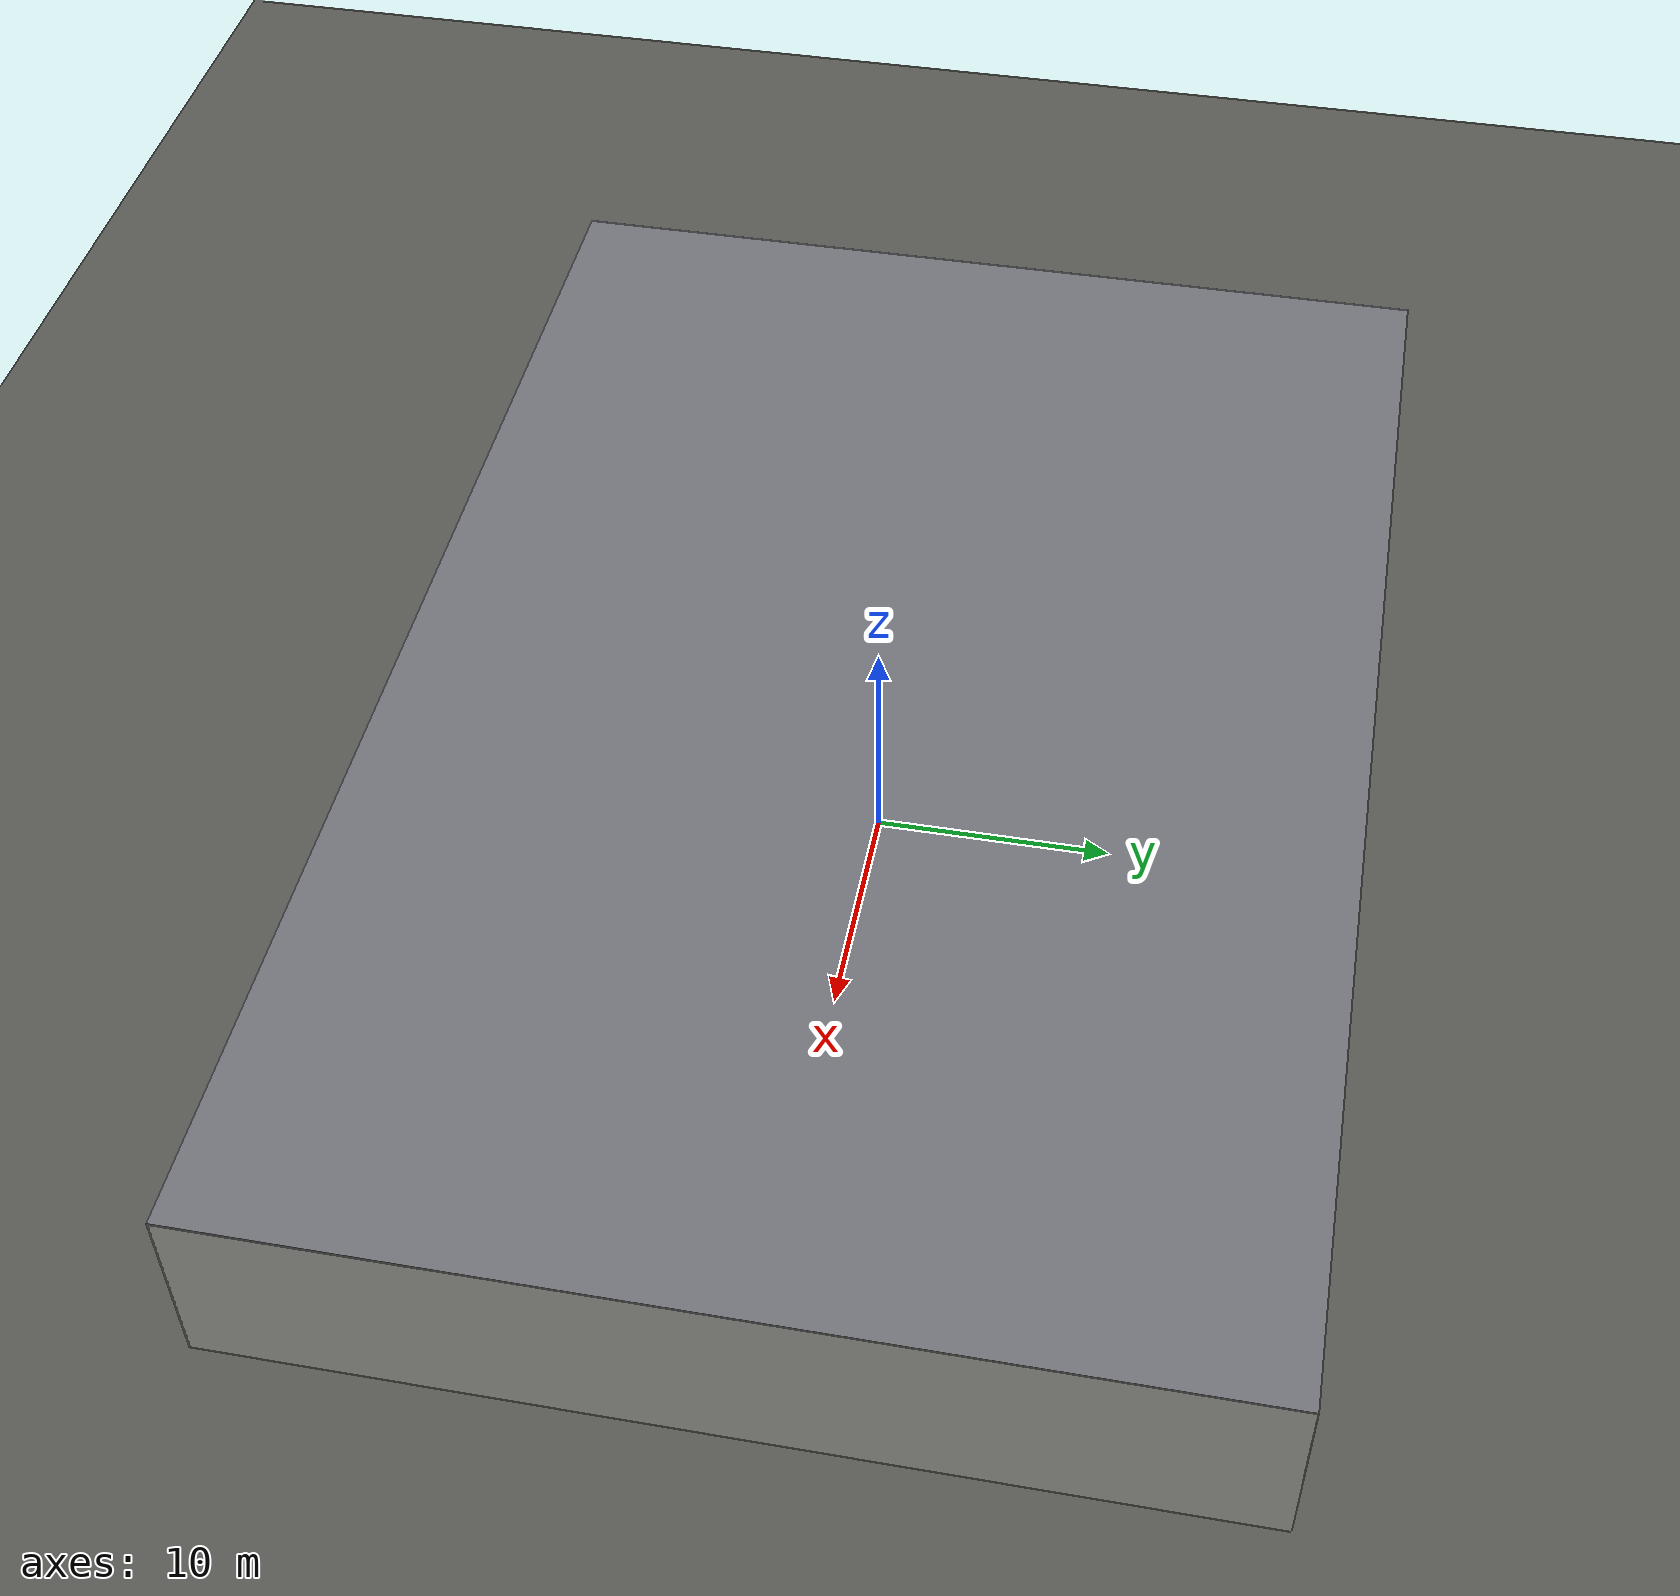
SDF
<sdf version="1.8">
 <world name="warehouse">
  <physics name="1ms" type="ode">
   <max_step_size>0.001</max_step_size>
   <real_time_factor>1.0</real_time_factor>
   <real_time_update_rate>1000</real_time_update_rate>
  </physics>
  <plugin filename="ignition-gazebo-physics-system" name="ignition::gazebo::systems::Physics"/>
  <plugin filename="ignition-gazebo-user-commands-system" name="ignition::gazebo::systems::UserCommands"/>
  <plugin filename="ignition-gazebo-scene-broadcaster-system" name="ignition::gazebo::systems::SceneBroadcaster"/>
  <plugin filename="ignition-gazebo-sensors-system" name="ignition::gazebo::systems::Sensors">
   <render_engine>ogre2</render_engine>
  </plugin>
  <plugin filename="ignition-gazebo-imu-system" name="ignition::gazebo::systems::Imu"/>
  <plugin filename="ignition-gazebo-contact-system" name="ignition::gazebo::systems::Contact"/>
  <scene>
   <ambient>0.25 0.25 0.25 1</ambient>
   <background>0.35 0.37 0.40 1</background>
   <shadows>true</shadows>
  </scene>
  <light type="directional" name="sun">
   <visualize>false</visualize>
   <pose>0 0 12 0 0 0</pose>
   <diffuse>0.35 0.35 0.35 1</diffuse>
   <specular>0.1 0.1 0.1 1</specular>
   <direction>-0.3 0.2 -0.9</direction>
  </light>
  <light type="point" name="highbay_0">
   <cast_shadows>false</cast_shadows>
   <visualize>false</visualize>
   <pose>-18.0000 15.0000 7.0000 0.0000 0.0000 0.0000</pose>
   <diffuse>0.75 0.75 0.70 1</diffuse>
   <specular>0.1 0.1 0.1 1</specular>
   <attenuation>
    <range>25</range>
    <constant>0.3</constant>
    <linear>0.02</linear>
    <quadratic>0.004</quadratic>
   </attenuation>
  </light>
  <light type="point" name="highbay_1">
   <cast_shadows>false</cast_shadows>
   <visualize>false</visualize>
   <pose>18.0000 15.0000 7.0000 0.0000 0.0000 0.0000</pose>
   <diffuse>0.75 0.75 0.70 1</diffuse>
   <specular>0.1 0.1 0.1 1</specular>
   <attenuation>
    <range>25</range>
    <constant>0.3</constant>
    <linear>0.02</linear>
    <quadratic>0.004</quadratic>
   </attenuation>
  </light>
  <light type="point" name="highbay_2">
   <cast_shadows>false</cast_shadows>
   <visualize>false</visualize>
   <pose>-18.0000 6.0000 7.0000 0.0000 0.0000 0.0000</pose>
   <diffuse>0.75 0.75 0.70 1</diffuse>
   <specular>0.1 0.1 0.1 1</specular>
   <attenuation>
    <range>25</range>
    <constant>0.3</constant>
    <linear>0.02</linear>
    <quadratic>0.004</quadratic>
   </attenuation>
  </light>
  <light type="point" name="highbay_3">
   <cast_shadows>false</cast_shadows>
   <visualize>false</visualize>
   <pose>-6.0000 6.0000 7.0000 0.0000 0.0000 0.0000</pose>
   <diffuse>0.75 0.75 0.70 1</diffuse>
   <specular>0.1 0.1 0.1 1</specular>
   <attenuation>
    <range>25</range>
    <constant>0.3</constant>
    <linear>0.02</linear>
    <quadratic>0.004</quadratic>
   </attenuation>
  </light>
  <light type="point" name="highbay_4">
   <cast_shadows>false</cast_shadows>
   <visualize>false</visualize>
   <pose>6.0000 6.0000 7.0000 0.0000 0.0000 0.0000</pose>
   <diffuse>0.75 0.75 0.70 1</diffuse>
   <specular>0.1 0.1 0.1 1</specular>
   <attenuation>
    <range>25</range>
    <constant>0.3</constant>
    <linear>0.02</linear>
    <quadratic>0.004</quadratic>
   </attenuation>
  </light>
  <light type="point" name="highbay_5">
   <cast_shadows>false</cast_shadows>
   <visualize>false</visualize>
   <pose>18.0000 6.0000 7.0000 0.0000 0.0000 0.0000</pose>
   <diffuse>0.75 0.75 0.70 1</diffuse>
   <specular>0.1 0.1 0.1 1</specular>
   <attenuation>
    <range>25</range>
    <constant>0.3</constant>
    <linear>0.02</linear>
    <quadratic>0.004</quadratic>
   </attenuation>
  </light>
  <light type="point" name="highbay_6">
   <cast_shadows>false</cast_shadows>
   <visualize>false</visualize>
   <pose>-18.0000 -6.0000 7.0000 0.0000 0.0000 0.0000</pose>
   <diffuse>0.75 0.75 0.70 1</diffuse>
   <specular>0.1 0.1 0.1 1</specular>
   <attenuation>
    <range>25</range>
    <constant>0.3</constant>
    <linear>0.02</linear>
    <quadratic>0.004</quadratic>
   </attenuation>
  </light>
  <light type="point" name="highbay_7">
   <cast_shadows>false</cast_shadows>
   <visualize>false</visualize>
   <pose>-6.0000 -6.0000 7.0000 0.0000 0.0000 0.0000</pose>
   <diffuse>0.75 0.75 0.70 1</diffuse>
   <specular>0.1 0.1 0.1 1</specular>
   <attenuation>
    <range>25</range>
    <constant>0.3</constant>
    <linear>0.02</linear>
    <quadratic>0.004</quadratic>
   </attenuation>
  </light>
  <light type="point" name="highbay_8">
   <cast_shadows>false</cast_shadows>
   <visualize>false</visualize>
   <pose>6.0000 -6.0000 7.0000 0.0000 0.0000 0.0000</pose>
   <diffuse>0.75 0.75 0.70 1</diffuse>
   <specular>0.1 0.1 0.1 1</specular>
   <attenuation>
    <range>25</range>
    <constant>0.3</constant>
    <linear>0.02</linear>
    <quadratic>0.004</quadratic>
   </attenuation>
  </light>
  <light type="point" name="highbay_9">
   <cast_shadows>false</cast_shadows>
   <visualize>false</visualize>
   <pose>18.0000 -6.0000 7.0000 0.0000 0.0000 0.0000</pose>
   <diffuse>0.75 0.75 0.70 1</diffuse>
   <specular>0.1 0.1 0.1 1</specular>
   <attenuation>
    <range>25</range>
    <constant>0.3</constant>
    <linear>0.02</linear>
    <quadratic>0.004</quadratic>
   </attenuation>
  </light>
  <light type="point" name="highbay_10">
   <cast_shadows>false</cast_shadows>
   <visualize>false</visualize>
   <pose>-18.0000 -15.0000 7.0000 0.0000 0.0000 0.0000</pose>
   <diffuse>0.75 0.75 0.70 1</diffuse>
   <specular>0.1 0.1 0.1 1</specular>
   <attenuation>
    <range>25</range>
    <constant>0.3</constant>
    <linear>0.02</linear>
    <quadratic>0.004</quadratic>
   </attenuation>
  </light>
  <light type="point" name="highbay_11">
   <cast_shadows>false</cast_shadows>
   <visualize>false</visualize>
   <pose>18.0000 -15.0000 7.0000 0.0000 0.0000 0.0000</pose>
   <diffuse>0.75 0.75 0.70 1</diffuse>
   <specular>0.1 0.1 0.1 1</specular>
   <attenuation>
    <range>25</range>
    <constant>0.3</constant>
    <linear>0.02</linear>
    <quadratic>0.004</quadratic>
   </attenuation>
  </light>
  <model name="ground_plane">
   <static>true</static>
   <link name="link">
    <collision name="collision">
     <geometry><plane><normal>0 0 1</normal><size>64 44</size></plane></geometry>
     <surface><friction><ode><mu>0.8</mu><mu2>0.8</mu2></ode></friction></surface>
    </collision>
    <visual name="visual">
     <geometry><plane><normal>0 0 1</normal><size>64 44</size></plane></geometry>
     <material>
      <ambient>0.35 0.35 0.33 1</ambient>
      <diffuse>0.35 0.35 0.33 1</diffuse>
      <specular>0.05 0.05 0.05 1</specular>
     </material>
    </visual>
   </link>
  </model>
  <model name="warehouse_walls">
   <static>true</static>
   <link name="link">
    <collision name="wall_north_collision">
     <pose>0.0000 20.1000 4.0000 0.0000 0.0000 0.0000</pose>
     <geometry><box><size>60.4 0.2 8.0</size></box></geometry>
    </collision>
    <visual name="wall_north">
     <pose>0.0000 20.1000 4.0000 0.0000 0.0000 0.0000</pose>
     <geometry><box><size>60.4 0.2 8.0</size></box></geometry>
     <material><ambient>0.72 0.72 0.70 1</ambient><diffuse>0.72 0.72 0.70 1</diffuse></material>
    </visual>
    <collision name="wall_south_collision">
     <pose>0.0000 -20.1000 4.0000 0.0000 0.0000 0.0000</pose>
     <geometry><box><size>60.4 0.2 8.0</size></box></geometry>
    </collision>
    <visual name="wall_south">
     <pose>0.0000 -20.1000 4.0000 0.0000 0.0000 0.0000</pose>
     <geometry><box><size>60.4 0.2 8.0</size></box></geometry>
     <material><ambient>0.72 0.72 0.70 1</ambient><diffuse>0.72 0.72 0.70 1</diffuse></material>
    </visual>
    <collision name="wall_east_collision">
     <pose>30.1000 0.0000 4.0000 0.0000 0.0000 0.0000</pose>
     <geometry><box><size>0.2 40.4 8.0</size></box></geometry>
    </collision>
    <visual name="wall_east">
     <pose>30.1000 0.0000 4.0000 0.0000 0.0000 0.0000</pose>
     <geometry><box><size>0.2 40.4 8.0</size></box></geometry>
     <material><ambient>0.72 0.72 0.70 1</ambient><diffuse>0.72 0.72 0.70 1</diffuse></material>
    </visual>
    <collision name="wall_west_collision">
     <pose>-30.1000 0.0000 4.0000 0.0000 0.0000 0.0000</pose>
     <geometry><box><size>0.2 40.4 8.0</size></box></geometry>
    </collision>
    <visual name="wall_west">
     <pose>-30.1000 0.0000 4.0000 0.0000 0.0000 0.0000</pose>
     <geometry><box><size>0.2 40.4 8.0</size></box></geometry>
     <material><ambient>0.72 0.72 0.70 1</ambient><diffuse>0.72 0.72 0.70 1</diffuse></material>
    </visual>
   </link>
  </model>
  <model name="roof">
   <static>true</static>
   <link name="link">
    <visual name="ceiling">
     <pose>0.0000 0.0000 8.0000 0.0000 0.0000 0.0000</pose>
     <cast_shadows>false</cast_shadows>
     <geometry><plane><normal>0 0 -1</normal><size>60.4 40.4</size></plane></geometry>
     <material><ambient>0.45 0.46 0.48 1</ambient><diffuse>0.45 0.46 0.48 1</diffuse></material>
    </visual>
    <visual name="luminaire_0">
     <pose>-18.0000 15.0000 7.2500 0.0000 0.0000 0.0000</pose>
     <cast_shadows>false</cast_shadows>
     <geometry><box><size>1.2 0.4 0.08</size></box></geometry>
     <material>
      <ambient>1 1 0.95 1</ambient>
      <diffuse>1 1 0.95 1</diffuse>
      <emissive>0.9 0.9 0.85 1</emissive>
     </material>
    </visual>
    <visual name="luminaire_1">
     <pose>18.0000 15.0000 7.2500 0.0000 0.0000 0.0000</pose>
     <cast_shadows>false</cast_shadows>
     <geometry><box><size>1.2 0.4 0.08</size></box></geometry>
     <material>
      <ambient>1 1 0.95 1</ambient>
      <diffuse>1 1 0.95 1</diffuse>
      <emissive>0.9 0.9 0.85 1</emissive>
     </material>
    </visual>
    <visual name="luminaire_2">
     <pose>-18.0000 6.0000 7.2500 0.0000 0.0000 0.0000</pose>
     <cast_shadows>false</cast_shadows>
     <geometry><box><size>1.2 0.4 0.08</size></box></geometry>
     <material>
      <ambient>1 1 0.95 1</ambient>
      <diffuse>1 1 0.95 1</diffuse>
      <emissive>0.9 0.9 0.85 1</emissive>
     </material>
    </visual>
    <visual name="luminaire_3">
     <pose>-6.0000 6.0000 7.2500 0.0000 0.0000 0.0000</pose>
     <cast_shadows>false</cast_shadows>
     <geometry><box><size>1.2 0.4 0.08</size></box></geometry>
     <material>
      <ambient>1 1 0.95 1</ambient>
      <diffuse>1 1 0.95 1</diffuse>
      <emissive>0.9 0.9 0.85 1</emissive>
     </material>
    </visual>
    <visual name="luminaire_4">
     <pose>6.0000 6.0000 7.2500 0.0000 0.0000 0.0000</pose>
     <cast_shadows>false</cast_shadows>
     <geometry><box><size>1.2 0.4 0.08</size></box></geometry>
     <material>
      <ambient>1 1 0.95 1</ambient>
      <diffuse>1 1 0.95 1</diffuse>
      <emissive>0.9 0.9 0.85 1</emissive>
     </material>
    </visual>
    <visual name="luminaire_5">
     <pose>18.0000 6.0000 7.2500 0.0000 0.0000 0.0000</pose>
     <cast_shadows>false</cast_shadows>
     <geometry><box><size>1.2 0.4 0.08</size></box></geometry>
     <material>
      <ambient>1 1 0.95 1</ambient>
      <diffuse>1 1 0.95 1</diffuse>
      <emissive>0.9 0.9 0.85 1</emissive>
     </material>
    </visual>
    <visual name="luminaire_6">
     <pose>-18.0000 -6.0000 7.2500 0.0000 0.0000 0.0000</pose>
     <cast_shadows>false</cast_shadows>
     <geometry><box><size>1.2 0.4 0.08</size></box></geometry>
     <material>
      <ambient>1 1 0.95 1</ambient>
      <diffuse>1 1 0.95 1</diffuse>
      <emissive>0.9 0.9 0.85 1</emissive>
     </material>
    </visual>
    <visual name="luminaire_7">
     <pose>-6.0000 -6.0000 7.2500 0.0000 0.0000 0.0000</pose>
     <cast_shadows>false</cast_shadows>
     <geometry><box><size>1.2 0.4 0.08</size></box></geometry>
     <material>
      <ambient>1 1 0.95 1</ambient>
      <diffuse>1 1 0.95 1</diffuse>
      <emissive>0.9 0.9 0.85 1</emissive>
     </material>
    </visual>
    <visual name="luminaire_8">
     <pose>6.0000 -6.0000 7.2500 0.0000 0.0000 0.0000</pose>
     <cast_shadows>false</cast_shadows>
     <geometry><box><size>1.2 0.4 0.08</size></box></geometry>
     <material>
      <ambient>1 1 0.95 1</ambient>
      <diffuse>1 1 0.95 1</diffuse>
      <emissive>0.9 0.9 0.85 1</emissive>
     </material>
    </visual>
    <visual name="luminaire_9">
     <pose>18.0000 -6.0000 7.2500 0.0000 0.0000 0.0000</pose>
     <cast_shadows>false</cast_shadows>
     <geometry><box><size>1.2 0.4 0.08</size></box></geometry>
     <material>
      <ambient>1 1 0.95 1</ambient>
      <diffuse>1 1 0.95 1</diffuse>
      <emissive>0.9 0.9 0.85 1</emissive>
     </material>
    </visual>
    <visual name="luminaire_10">
     <pose>-18.0000 -15.0000 7.2500 0.0000 0.0000 0.0000</pose>
     <cast_shadows>false</cast_shadows>
     <geometry><box><size>1.2 0.4 0.08</size></box></geometry>
     <material>
      <ambient>1 1 0.95 1</ambient>
      <diffuse>1 1 0.95 1</diffuse>
      <emissive>0.9 0.9 0.85 1</emissive>
     </material>
    </visual>
    <visual name="luminaire_11">
     <pose>18.0000 -15.0000 7.2500 0.0000 0.0000 0.0000</pose>
     <cast_shadows>false</cast_shadows>
     <geometry><box><size>1.2 0.4 0.08</size></box></geometry>
     <material>
      <ambient>1 1 0.95 1</ambient>
      <diffuse>1 1 0.95 1</diffuse>
      <emissive>0.9 0.9 0.85 1</emissive>
     </material>
    </visual>
   </link>
  </model>
  <include>
   <uri>model://pillar</uri>
   <name>pillar_1</name>
   <pose>-10.0000 12.0000 0.0000 0.0000 0.0000 0.0000</pose>
  </include>
  <include>
   <uri>model://pillar</uri>
   <name>pillar_2</name>
   <pose>10.0000 12.0000 0.0000 0.0000 0.0000 0.0000</pose>
  </include>
  <include>
   <uri>model://pillar</uri>
   <name>pillar_3</name>
   <pose>-10.0000 -12.0000 0.0000 0.0000 0.0000 0.0000</pose>
  </include>
  <include>
   <uri>model://pillar</uri>
   <name>pillar_4</name>
   <pose>10.0000 -12.0000 0.0000 0.0000 0.0000 0.0000</pose>
  </include>
  <include>
   <uri>model://pillar</uri>
   <name>pillar_5</name>
   <pose>-25.0000 6.0000 0.0000 0.0000 0.0000 0.0000</pose>
  </include>
  <include>
   <uri>model://pillar</uri>
   <name>pillar_6</name>
   <pose>25.0000 6.0000 0.0000 0.0000 0.0000 0.0000</pose>
  </include>
  <include>
   <uri>model://pillar</uri>
   <name>pillar_7</name>
   <pose>-25.0000 -6.0000 0.0000 0.0000 0.0000 0.0000</pose>
  </include>
  <include>
   <uri>model://pillar</uri>
   <name>pillar_8</name>
   <pose>25.0000 -6.0000 0.0000 0.0000 0.0000 0.0000</pose>
  </include>
  <model name="pillar_1_marker_0">
   <static>true</static>
   <pose>-9.7380 12.0000 0.0000 0.0000 0.0000 0.0000</pose>
   <link name="link">
    <collision name="plate_collision">
     <pose>0 0 0.250 0 0 0</pose>
     <geometry><box><size>0.02 0.50 0.50</size></box></geometry>
    </collision>
    <visual name="plate">
     <pose>0 0 0.250 0 0 0</pose>
     <geometry><box><size>0.02 0.50 0.50</size></box></geometry>
     <material>
      <ambient>1 1 1 1</ambient>
      <diffuse>1 1 1 1</diffuse>
      <specular>0.05 0.05 0.05 1</specular>
      <pbr>
       <metal>
        <albedo_map>model://dock_marker/materials/textures/aruco_4x4_100_10.png</albedo_map>
        <metalness>0.0</metalness>
        <roughness>0.9</roughness>
       </metal>
      </pbr>
     </material>
    </visual>
   </link>
  </model>
  <model name="pillar_1_marker_1">
   <static>true</static>
   <pose>-10.2620 12.0000 0.0000 0.0000 0.0000 3.1416</pose>
   <link name="link">
    <collision name="plate_collision">
     <pose>0 0 0.250 0 0 0</pose>
     <geometry><box><size>0.02 0.50 0.50</size></box></geometry>
    </collision>
    <visual name="plate">
     <pose>0 0 0.250 0 0 0</pose>
     <geometry><box><size>0.02 0.50 0.50</size></box></geometry>
     <material>
      <ambient>1 1 1 1</ambient>
      <diffuse>1 1 1 1</diffuse>
      <specular>0.05 0.05 0.05 1</specular>
      <pbr>
       <metal>
        <albedo_map>model://dock_marker/materials/textures/aruco_4x4_100_11.png</albedo_map>
        <metalness>0.0</metalness>
        <roughness>0.9</roughness>
       </metal>
      </pbr>
     </material>
    </visual>
   </link>
  </model>
  <model name="pillar_1_marker_2">
   <static>true</static>
   <pose>-10.0000 12.2620 0.0000 0.0000 0.0000 1.5708</pose>
   <link name="link">
    <collision name="plate_collision">
     <pose>0 0 0.250 0 0 0</pose>
     <geometry><box><size>0.02 0.50 0.50</size></box></geometry>
    </collision>
    <visual name="plate">
     <pose>0 0 0.250 0 0 0</pose>
     <geometry><box><size>0.02 0.50 0.50</size></box></geometry>
     <material>
      <ambient>1 1 1 1</ambient>
      <diffuse>1 1 1 1</diffuse>
      <specular>0.05 0.05 0.05 1</specular>
      <pbr>
       <metal>
        <albedo_map>model://dock_marker/materials/textures/aruco_4x4_100_12.png</albedo_map>
        <metalness>0.0</metalness>
        <roughness>0.9</roughness>
       </metal>
      </pbr>
     </material>
    </visual>
   </link>
  </model>
  <model name="pillar_1_marker_3">
   <static>true</static>
   <pose>-10.0000 11.7380 0.0000 0.0000 0.0000 -1.5708</pose>
   <link name="link">
    <collision name="plate_collision">
     <pose>0 0 0.250 0 0 0</pose>
     <geometry><box><size>0.02 0.50 0.50</size></box></geometry>
    </collision>
    <visual name="plate">
     <pose>0 0 0.250 0 0 0</pose>
     <geometry><box><size>0.02 0.50 0.50</size></box></geometry>
     <material>
      <ambient>1 1 1 1</ambient>
      <diffuse>1 1 1 1</diffuse>
      <specular>0.05 0.05 0.05 1</specular>
      <pbr>
       <metal>
        <albedo_map>model://dock_marker/materials/textures/aruco_4x4_100_13.png</albedo_map>
        <metalness>0.0</metalness>
        <roughness>0.9</roughness>
       </metal>
      </pbr>
     </material>
    </visual>
   </link>
  </model>
  <model name="pillar_2_marker_0">
   <static>true</static>
   <pose>10.2620 12.0000 0.0000 0.0000 0.0000 0.0000</pose>
   <link name="link">
    <collision name="plate_collision">
     <pose>0 0 0.250 0 0 0</pose>
     <geometry><box><size>0.02 0.50 0.50</size></box></geometry>
    </collision>
    <visual name="plate">
     <pose>0 0 0.250 0 0 0</pose>
     <geometry><box><size>0.02 0.50 0.50</size></box></geometry>
     <material>
      <ambient>1 1 1 1</ambient>
      <diffuse>1 1 1 1</diffuse>
      <specular>0.05 0.05 0.05 1</specular>
      <pbr>
       <metal>
        <albedo_map>model://dock_marker/materials/textures/aruco_4x4_100_14.png</albedo_map>
        <metalness>0.0</metalness>
        <roughness>0.9</roughness>
       </metal>
      </pbr>
     </material>
    </visual>
   </link>
  </model>
  <model name="pillar_2_marker_1">
   <static>true</static>
   <pose>9.7380 12.0000 0.0000 0.0000 0.0000 3.1416</pose>
   <link name="link">
    <collision name="plate_collision">
     <pose>0 0 0.250 0 0 0</pose>
     <geometry><box><size>0.02 0.50 0.50</size></box></geometry>
    </collision>
    <visual name="plate">
     <pose>0 0 0.250 0 0 0</pose>
     <geometry><box><size>0.02 0.50 0.50</size></box></geometry>
     <material>
      <ambient>1 1 1 1</ambient>
      <diffuse>1 1 1 1</diffuse>
      <specular>0.05 0.05 0.05 1</specular>
      <pbr>
       <metal>
        <albedo_map>model://dock_marker/materials/textures/aruco_4x4_100_15.png</albedo_map>
        <metalness>0.0</metalness>
        <roughness>0.9</roughness>
       </metal>
      </pbr>
     </material>
    </visual>
   </link>
  </model>
  <model name="pillar_2_marker_2">
   <static>true</static>
   <pose>10.0000 12.2620 0.0000 0.0000 0.0000 1.5708</pose>
   <link name="link">
    <collision name="plate_collision">
     <pose>0 0 0.250 0 0 0</pose>
     <geometry><box><size>0.02 0.50 0.50</size></box></geometry>
    </collision>
    <visual name="plate">
     <pose>0 0 0.250 0 0 0</pose>
     <geometry><box><size>0.02 0.50 0.50</size></box></geometry>
     <material>
      <ambient>1 1 1 1</ambient>
      <diffuse>1 1 1 1</diffuse>
      <specular>0.05 0.05 0.05 1</specular>
      <pbr>
       <metal>
        <albedo_map>model://dock_marker/materials/textures/aruco_4x4_100_16.png</albedo_map>
        <metalness>0.0</metalness>
        <roughness>0.9</roughness>
       </metal>
      </pbr>
     </material>
    </visual>
   </link>
  </model>
  <model name="pillar_2_marker_3">
   <static>true</static>
   <pose>10.0000 11.7380 0.0000 0.0000 0.0000 -1.5708</pose>
   <link name="link">
    <collision name="plate_collision">
     <pose>0 0 0.250 0 0 0</pose>
     <geometry><box><size>0.02 0.50 0.50</size></box></geometry>
    </collision>
    <visual name="plate">
     <pose>0 0 0.250 0 0 0</pose>
     <geometry><box><size>0.02 0.50 0.50</size></box></geometry>
     <material>
      <ambient>1 1 1 1</ambient>
      <diffuse>1 1 1 1</diffuse>
      <specular>0.05 0.05 0.05 1</specular>
      <pbr>
       <metal>
        <albedo_map>model://dock_marker/materials/textures/aruco_4x4_100_17.png</albedo_map>
        <metalness>0.0</metalness>
        <roughness>0.9</roughness>
       </metal>
      </pbr>
     </material>
    </visual>
   </link>
  </model>
  <model name="pillar_3_marker_0">
   <static>true</static>
   <pose>-9.7380 -12.0000 0.0000 0.0000 0.0000 0.0000</pose>
   <link name="link">
    <collision name="plate_collision">
     <pose>0 0 0.250 0 0 0</pose>
     <geometry><box><size>0.02 0.50 0.50</size></box></geometry>
    </collision>
    <visual name="plate">
     <pose>0 0 0.250 0 0 0</pose>
     <geometry><box><size>0.02 0.50 0.50</size></box></geometry>
     <material>
      <ambient>1 1 1 1</ambient>
      <diffuse>1 1 1 1</diffuse>
      <specular>0.05 0.05 0.05 1</specular>
      <pbr>
       <metal>
        <albedo_map>model://dock_marker/materials/textures/aruco_4x4_100_18.png</albedo_map>
        <metalness>0.0</metalness>
        <roughness>0.9</roughness>
       </metal>
      </pbr>
     </material>
    </visual>
   </link>
  </model>
  <model name="pillar_3_marker_1">
   <static>true</static>
   <pose>-10.2620 -12.0000 0.0000 0.0000 0.0000 3.1416</pose>
   <link name="link">
    <collision name="plate_collision">
     <pose>0 0 0.250 0 0 0</pose>
     <geometry><box><size>0.02 0.50 0.50</size></box></geometry>
    </collision>
    <visual name="plate">
     <pose>0 0 0.250 0 0 0</pose>
     <geometry><box><size>0.02 0.50 0.50</size></box></geometry>
     <material>
      <ambient>1 1 1 1</ambient>
      <diffuse>1 1 1 1</diffuse>
      <specular>0.05 0.05 0.05 1</specular>
      <pbr>
       <metal>
        <albedo_map>model://dock_marker/materials/textures/aruco_4x4_100_19.png</albedo_map>
        <metalness>0.0</metalness>
        <roughness>0.9</roughness>
       </metal>
      </pbr>
     </material>
    </visual>
   </link>
  </model>
  <model name="pillar_3_marker_2">
   <static>true</static>
   <pose>-10.0000 -11.7380 0.0000 0.0000 0.0000 1.5708</pose>
   <link name="link">
    <collision name="plate_collision">
     <pose>0 0 0.250 0 0 0</pose>
     <geometry><box><size>0.02 0.50 0.50</size></box></geometry>
    </collision>
    <visual name="plate">
     <pose>0 0 0.250 0 0 0</pose>
     <geometry><box><size>0.02 0.50 0.50</size></box></geometry>
     <material>
      <ambient>1 1 1 1</ambient>
      <diffuse>1 1 1 1</diffuse>
      <specular>0.05 0.05 0.05 1</specular>
      <pbr>
       <metal>
        <albedo_map>model://dock_marker/materials/textures/aruco_4x4_100_20.png</albedo_map>
        <metalness>0.0</metalness>
        <roughness>0.9</roughness>
       </metal>
      </pbr>
     </material>
    </visual>
   </link>
  </model>
  <model name="pillar_3_marker_3">
   <static>true</static>
   <pose>-10.0000 -12.2620 0.0000 0.0000 0.0000 -1.5708</pose>
   <link name="link">
    <collision name="plate_collision">
     <pose>0 0 0.250 0 0 0</pose>
     <geometry><box><size>0.02 0.50 0.50</size></box></geometry>
    </collision>
    <visual name="plate">
     <pose>0 0 0.250 0 0 0</pose>
     <geometry><box><size>0.02 0.50 0.50</size></box></geometry>
     <material>
      <ambient>1 1 1 1</ambient>
      <diffuse>1 1 1 1</diffuse>
      <specular>0.05 0.05 0.05 1</specular>
      <pbr>
       <metal>
        <albedo_map>model://dock_marker/materials/textures/aruco_4x4_100_21.png</albedo_map>
        <metalness>0.0</metalness>
        <roughness>0.9</roughness>
       </metal>
      </pbr>
     </material>
    </visual>
   </link>
  </model>
  <model name="pillar_4_marker_0">
   <static>true</static>
   <pose>10.2620 -12.0000 0.0000 0.0000 0.0000 0.0000</pose>
   <link name="link">
    <collision name="plate_collision">
     <pose>0 0 0.250 0 0 0</pose>
     <geometry><box><size>0.02 0.50 0.50</size></box></geometry>
    </collision>
    <visual name="plate">
     <pose>0 0 0.250 0 0 0</pose>
     <geometry><box><size>0.02 0.50 0.50</size></box></geometry>
     <material>
      <ambient>1 1 1 1</ambient>
      <diffuse>1 1 1 1</diffuse>
      <specular>0.05 0.05 0.05 1</specular>
      <pbr>
       <metal>
        <albedo_map>model://dock_marker/materials/textures/aruco_4x4_100_22.png</albedo_map>
        <metalness>0.0</metalness>
        <roughness>0.9</roughness>
       </metal>
      </pbr>
     </material>
    </visual>
   </link>
  </model>
  <model name="pillar_4_marker_1">
   <static>true</static>
   <pose>9.7380 -12.0000 0.0000 0.0000 0.0000 3.1416</pose>
   <link name="link">
    <collision name="plate_collision">
     <pose>0 0 0.250 0 0 0</pose>
     <geometry><box><size>0.02 0.50 0.50</size></box></geometry>
    </collision>
    <visual name="plate">
     <pose>0 0 0.250 0 0 0</pose>
     <geometry><box><size>0.02 0.50 0.50</size></box></geometry>
     <material>
      <ambient>1 1 1 1</ambient>
      <diffuse>1 1 1 1</diffuse>
      <specular>0.05 0.05 0.05 1</specular>
      <pbr>
       <metal>
        <albedo_map>model://dock_marker/materials/textures/aruco_4x4_100_23.png</albedo_map>
        <metalness>0.0</metalness>
        <roughness>0.9</roughness>
       </metal>
      </pbr>
     </material>
    </visual>
   </link>
  </model>
  <model name="pillar_4_marker_2">
   <static>true</static>
   <pose>10.0000 -11.7380 0.0000 0.0000 0.0000 1.5708</pose>
   <link name="link">
    <collision name="plate_collision">
     <pose>0 0 0.250 0 0 0</pose>
     <geometry><box><size>0.02 0.50 0.50</size></box></geometry>
    </collision>
    <visual name="plate">
     <pose>0 0 0.250 0 0 0</pose>
     <geometry><box><size>0.02 0.50 0.50</size></box></geometry>
     <material>
      <ambient>1 1 1 1</ambient>
      <diffuse>1 1 1 1</diffuse>
      <specular>0.05 0.05 0.05 1</specular>
      <pbr>
       <metal>
        <albedo_map>model://dock_marker/materials/textures/aruco_4x4_100_24.png</albedo_map>
        <metalness>0.0</metalness>
        <roughness>0.9</roughness>
       </metal>
      </pbr>
     </material>
    </visual>
   </link>
  </model>
  <model name="pillar_4_marker_3">
   <static>true</static>
   <pose>10.0000 -12.2620 0.0000 0.0000 0.0000 -1.5708</pose>
   <link name="link">
    <collision name="plate_collision">
     <pose>0 0 0.250 0 0 0</pose>
     <geometry><box><size>0.02 0.50 0.50</size></box></geometry>
    </collision>
    <visual name="plate">
     <pose>0 0 0.250 0 0 0</pose>
     <geometry><box><size>0.02 0.50 0.50</size></box></geometry>
     <material>
      <ambient>1 1 1 1</ambient>
      <diffuse>1 1 1 1</diffuse>
      <specular>0.05 0.05 0.05 1</specular>
      <pbr>
       <metal>
        <albedo_map>model://dock_marker/materials/textures/aruco_4x4_100_25.png</albedo_map>
        <metalness>0.0</metalness>
        <roughness>0.9</roughness>
       </metal>
      </pbr>
     </material>
    </visual>
   </link>
  </model>
  <model name="pillar_5_marker_0">
   <static>true</static>
   <pose>-24.7380 6.0000 0.0000 0.0000 0.0000 0.0000</pose>
   <link name="link">
    <collision name="plate_collision">
     <pose>0 0 0.250 0 0 0</pose>
     <geometry><box><size>0.02 0.50 0.50</size></box></geometry>
    </collision>
    <visual name="plate">
     <pose>0 0 0.250 0 0 0</pose>
     <geometry><box><size>0.02 0.50 0.50</size></box></geometry>
     <material>
      <ambient>1 1 1 1</ambient>
      <diffuse>1 1 1 1</diffuse>
      <specular>0.05 0.05 0.05 1</specular>
      <pbr>
       <metal>
        <albedo_map>model://dock_marker/materials/textures/aruco_4x4_100_26.png</albedo_map>
        <metalness>0.0</metalness>
        <roughness>0.9</roughness>
       </metal>
      </pbr>
     </material>
    </visual>
   </link>
  </model>
  <model name="pillar_5_marker_1">
   <static>true</static>
   <pose>-25.2620 6.0000 0.0000 0.0000 0.0000 3.1416</pose>
   <link name="link">
    <collision name="plate_collision">
     <pose>0 0 0.250 0 0 0</pose>
     <geometry><box><size>0.02 0.50 0.50</size></box></geometry>
    </collision>
    <visual name="plate">
     <pose>0 0 0.250 0 0 0</pose>
     <geometry><box><size>0.02 0.50 0.50</size></box></geometry>
     <material>
      <ambient>1 1 1 1</ambient>
      <diffuse>1 1 1 1</diffuse>
      <specular>0.05 0.05 0.05 1</specular>
      <pbr>
       <metal>
        <albedo_map>model://dock_marker/materials/textures/aruco_4x4_100_27.png</albedo_map>
        <metalness>0.0</metalness>
        <roughness>0.9</roughness>
       </metal>
      </pbr>
     </material>
    </visual>
   </link>
  </model>
  <model name="pillar_5_marker_2">
   <static>true</static>
   <pose>-25.0000 6.2620 0.0000 0.0000 0.0000 1.5708</pose>
   <link name="link">
    <collision name="plate_collision">
     <pose>0 0 0.250 0 0 0</pose>
     <geometry><box><size>0.02 0.50 0.50</size></box></geometry>
    </collision>
    <visual name="plate">
     <pose>0 0 0.250 0 0 0</pose>
     <geometry><box><size>0.02 0.50 0.50</size></box></geometry>
     <material>
      <ambient>1 1 1 1</ambient>
      <diffuse>1 1 1 1</diffuse>
      <specular>0.05 0.05 0.05 1</specular>
      <pbr>
       <metal>
        <albedo_map>model://dock_marker/materials/textures/aruco_4x4_100_28.png</albedo_map>
        <metalness>0.0</metalness>
        <roughness>0.9</roughness>
       </metal>
      </pbr>
     </material>
    </visual>
   </link>
  </model>
  <model name="pillar_5_marker_3">
   <static>true</static>
   <pose>-25.0000 5.7380 0.0000 0.0000 0.0000 -1.5708</pose>
   <link name="link">
    <collision name="plate_collision">
     <pose>0 0 0.250 0 0 0</pose>
     <geometry><box><size>0.02 0.50 0.50</size></box></geometry>
    </collision>
    <visual name="plate">
     <pose>0 0 0.250 0 0 0</pose>
     <geometry><box><size>0.02 0.50 0.50</size></box></geometry>
     <material>
      <ambient>1 1 1 1</ambient>
      <diffuse>1 1 1 1</diffuse>
      <specular>0.05 0.05 0.05 1</specular>
      <pbr>
       <metal>
        <albedo_map>model://dock_marker/materials/textures/aruco_4x4_100_29.png</albedo_map>
        <metalness>0.0</metalness>
        <roughness>0.9</roughness>
       </metal>
      </pbr>
     </material>
    </visual>
   </link>
  </model>
  <model name="pillar_6_marker_0">
   <static>true</static>
   <pose>25.2620 6.0000 0.0000 0.0000 0.0000 0.0000</pose>
   <link name="link">
    <collision name="plate_collision">
     <pose>0 0 0.250 0 0 0</pose>
     <geometry><box><size>0.02 0.50 0.50</size></box></geometry>
    </collision>
    <visual name="plate">
     <pose>0 0 0.250 0 0 0</pose>
     <geometry><box><size>0.02 0.50 0.50</size></box></geometry>
     <material>
      <ambient>1 1 1 1</ambient>
      <diffuse>1 1 1 1</diffuse>
      <specular>0.05 0.05 0.05 1</specular>
      <pbr>
       <metal>
        <albedo_map>model://dock_marker/materials/textures/aruco_4x4_100_30.png</albedo_map>
        <metalness>0.0</metalness>
        <roughness>0.9</roughness>
       </metal>
      </pbr>
     </material>
    </visual>
   </link>
  </model>
  <model name="pillar_6_marker_1">
   <static>true</static>
   <pose>24.7380 6.0000 0.0000 0.0000 0.0000 3.1416</pose>
   <link name="link">
    <collision name="plate_collision">
     <pose>0 0 0.250 0 0 0</pose>
     <geometry><box><size>0.02 0.50 0.50</size></box></geometry>
    </collision>
    <visual name="plate">
     <pose>0 0 0.250 0 0 0</pose>
     <geometry><box><size>0.02 0.50 0.50</size></box></geometry>
     <material>
      <ambient>1 1 1 1</ambient>
      <diffuse>1 1 1 1</diffuse>
      <specular>0.05 0.05 0.05 1</specular>
      <pbr>
       <metal>
        <albedo_map>model://dock_marker/materials/textures/aruco_4x4_100_31.png</albedo_map>
        <metalness>0.0</metalness>
        <roughness>0.9</roughness>
       </metal>
      </pbr>
     </material>
    </visual>
   </link>
  </model>
  <model name="pillar_6_marker_2">
   <static>true</static>
   <pose>25.0000 6.2620 0.0000 0.0000 0.0000 1.5708</pose>
   <link name="link">
    <collision name="plate_collision">
     <pose>0 0 0.250 0 0 0</pose>
     <geometry><box><size>0.02 0.50 0.50</size></box></geometry>
    </collision>
    <visual name="plate">
     <pose>0 0 0.250 0 0 0</pose>
     <geometry><box><size>0.02 0.50 0.50</size></box></geometry>
     <material>
      <ambient>1 1 1 1</ambient>
      <diffuse>1 1 1 1</diffuse>
      <specular>0.05 0.05 0.05 1</specular>
      <pbr>
       <metal>
        <albedo_map>model://dock_marker/materials/textures/aruco_4x4_100_32.png</albedo_map>
        <metalness>0.0</metalness>
        <roughness>0.9</roughness>
       </metal>
      </pbr>
     </material>
    </visual>
   </link>
  </model>
  <model name="pillar_6_marker_3">
   <static>true</static>
   <pose>25.0000 5.7380 0.0000 0.0000 0.0000 -1.5708</pose>
   <link name="link">
    <collision name="plate_collision">
     <pose>0 0 0.250 0 0 0</pose>
     <geometry><box><size>0.02 0.50 0.50</size></box></geometry>
    </collision>
    <visual name="plate">
     <pose>0 0 0.250 0 0 0</pose>
     <geometry><box><size>0.02 0.50 0.50</size></box></geometry>
     <material>
      <ambient>1 1 1 1</ambient>
      <diffuse>1 1 1 1</diffuse>
      <specular>0.05 0.05 0.05 1</specular>
      <pbr>
       <metal>
        <albedo_map>model://dock_marker/materials/textures/aruco_4x4_100_33.png</albedo_map>
        <metalness>0.0</metalness>
        <roughness>0.9</roughness>
       </metal>
      </pbr>
     </material>
    </visual>
   </link>
  </model>
  <model name="pillar_7_marker_0">
   <static>true</static>
   <pose>-24.7380 -6.0000 0.0000 0.0000 0.0000 0.0000</pose>
   <link name="link">
    <collision name="plate_collision">
     <pose>0 0 0.250 0 0 0</pose>
     <geometry><box><size>0.02 0.50 0.50</size></box></geometry>
    </collision>
    <visual name="plate">
     <pose>0 0 0.250 0 0 0</pose>
     <geometry><box><size>0.02 0.50 0.50</size></box></geometry>
     <material>
      <ambient>1 1 1 1</ambient>
      <diffuse>1 1 1 1</diffuse>
      <specular>0.05 0.05 0.05 1</specular>
      <pbr>
       <metal>
        <albedo_map>model://dock_marker/materials/textures/aruco_4x4_100_34.png</albedo_map>
        <metalness>0.0</metalness>
        <roughness>0.9</roughness>
       </metal>
      </pbr>
     </material>
    </visual>
   </link>
  </model>
  <model name="pillar_7_marker_1">
   <static>true</static>
   <pose>-25.2620 -6.0000 0.0000 0.0000 0.0000 3.1416</pose>
   <link name="link">
    <collision name="plate_collision">
     <pose>0 0 0.250 0 0 0</pose>
     <geometry><box><size>0.02 0.50 0.50</size></box></geometry>
    </collision>
    <visual name="plate">
     <pose>0 0 0.250 0 0 0</pose>
     <geometry><box><size>0.02 0.50 0.50</size></box></geometry>
     <material>
      <ambient>1 1 1 1</ambient>
      <diffuse>1 1 1 1</diffuse>
      <specular>0.05 0.05 0.05 1</specular>
      <pbr>
       <metal>
        <albedo_map>model://dock_marker/materials/textures/aruco_4x4_100_35.png</albedo_map>
        <metalness>0.0</metalness>
        <roughness>0.9</roughness>
       </metal>
      </pbr>
     </material>
    </visual>
   </link>
  </model>
  <model name="pillar_7_marker_2">
   <static>true</static>
   <pose>-25.0000 -5.7380 0.0000 0.0000 0.0000 1.5708</pose>
   <link name="link">
    <collision name="plate_collision">
     <pose>0 0 0.250 0 0 0</pose>
     <geometry><box><size>0.02 0.50 0.50</size></box></geometry>
    </collision>
    <visual name="plate">
     <pose>0 0 0.250 0 0 0</pose>
     <geometry><box><size>0.02 0.50 0.50</size></box></geometry>
     <material>
      <ambient>1 1 1 1</ambient>
      <diffuse>1 1 1 1</diffuse>
      <specular>0.05 0.05 0.05 1</specular>
      <pbr>
       <metal>
        <albedo_map>model://dock_marker/materials/textures/aruco_4x4_100_36.png</albedo_map>
        <metalness>0.0</metalness>
        <roughness>0.9</roughness>
       </metal>
      </pbr>
     </material>
    </visual>
   </link>
  </model>
  <model name="pillar_7_marker_3">
   <static>true</static>
   <pose>-25.0000 -6.2620 0.0000 0.0000 0.0000 -1.5708</pose>
   <link name="link">
    <collision name="plate_collision">
     <pose>0 0 0.250 0 0 0</pose>
     <geometry><box><size>0.02 0.50 0.50</size></box></geometry>
    </collision>
    <visual name="plate">
     <pose>0 0 0.250 0 0 0</pose>
     <geometry><box><size>0.02 0.50 0.50</size></box></geometry>
     <material>
      <ambient>1 1 1 1</ambient>
      <diffuse>1 1 1 1</diffuse>
      <specular>0.05 0.05 0.05 1</specular>
      <pbr>
       <metal>
        <albedo_map>model://dock_marker/materials/textures/aruco_4x4_100_37.png</albedo_map>
        <metalness>0.0</metalness>
        <roughness>0.9</roughness>
       </metal>
      </pbr>
     </material>
    </visual>
   </link>
  </model>
  <model name="pillar_8_marker_0">
   <static>true</static>
   <pose>25.2620 -6.0000 0.0000 0.0000 0.0000 0.0000</pose>
   <link name="link">
    <collision name="plate_collision">
     <pose>0 0 0.250 0 0 0</pose>
     <geometry><box><size>0.02 0.50 0.50</size></box></geometry>
    </collision>
    <visual name="plate">
     <pose>0 0 0.250 0 0 0</pose>
     <geometry><box><size>0.02 0.50 0.50</size></box></geometry>
     <material>
      <ambient>1 1 1 1</ambient>
      <diffuse>1 1 1 1</diffuse>
      <specular>0.05 0.05 0.05 1</specular>
      <pbr>
       <metal>
        <albedo_map>model://dock_marker/materials/textures/aruco_4x4_100_38.png</albedo_map>
        <metalness>0.0</metalness>
        <roughness>0.9</roughness>
       </metal>
      </pbr>
     </material>
    </visual>
   </link>
  </model>
  <model name="pillar_8_marker_1">
   <static>true</static>
   <pose>24.7380 -6.0000 0.0000 0.0000 0.0000 3.1416</pose>
   <link name="link">
    <collision name="plate_collision">
     <pose>0 0 0.250 0 0 0</pose>
     <geometry><box><size>0.02 0.50 0.50</size></box></geometry>
    </collision>
    <visual name="plate">
     <pose>0 0 0.250 0 0 0</pose>
     <geometry><box><size>0.02 0.50 0.50</size></box></geometry>
     <material>
      <ambient>1 1 1 1</ambient>
      <diffuse>1 1 1 1</diffuse>
      <specular>0.05 0.05 0.05 1</specular>
      <pbr>
       <metal>
        <albedo_map>model://dock_marker/materials/textures/aruco_4x4_100_39.png</albedo_map>
        <metalness>0.0</metalness>
        <roughness>0.9</roughness>
       </metal>
      </pbr>
     </material>
    </visual>
   </link>
  </model>
  <model name="pillar_8_marker_2">
   <static>true</static>
   <pose>25.0000 -5.7380 0.0000 0.0000 0.0000 1.5708</pose>
   <link name="link">
    <collision name="plate_collision">
     <pose>0 0 0.250 0 0 0</pose>
     <geometry><box><size>0.02 0.50 0.50</size></box></geometry>
    </collision>
    <visual name="plate">
     <pose>0 0 0.250 0 0 0</pose>
     <geometry><box><size>0.02 0.50 0.50</size></box></geometry>
     <material>
      <ambient>1 1 1 1</ambient>
      <diffuse>1 1 1 1</diffuse>
      <specular>0.05 0.05 0.05 1</specular>
      <pbr>
       <metal>
        <albedo_map>model://dock_marker/materials/textures/aruco_4x4_100_40.png</albedo_map>
        <metalness>0.0</metalness>
        <roughness>0.9</roughness>
       </metal>
      </pbr>
     </material>
    </visual>
   </link>
  </model>
  <model name="pillar_8_marker_3">
   <static>true</static>
   <pose>25.0000 -6.2620 0.0000 0.0000 0.0000 -1.5708</pose>
   <link name="link">
    <collision name="plate_collision">
     <pose>0 0 0.250 0 0 0</pose>
     <geometry><box><size>0.02 0.50 0.50</size></box></geometry>
    </collision>
    <visual name="plate">
     <pose>0 0 0.250 0 0 0</pose>
     <geometry><box><size>0.02 0.50 0.50</size></box></geometry>
     <material>
      <ambient>1 1 1 1</ambient>
      <diffuse>1 1 1 1</diffuse>
      <specular>0.05 0.05 0.05 1</specular>
      <pbr>
       <metal>
        <albedo_map>model://dock_marker/materials/textures/aruco_4x4_100_41.png</albedo_map>
        <metalness>0.0</metalness>
        <roughness>0.9</roughness>
       </metal>
      </pbr>
     </material>
    </visual>
   </link>
  </model>
  <model name="rack_marker_42">
   <static>true</static>
   <pose>-18.0000 9.5120 0.0000 0.0000 0.0000 1.5708</pose>
   <link name="link">
    <collision name="plate_collision">
     <pose>0 0 0.250 0 0 0</pose>
     <geometry><box><size>0.02 0.50 0.50</size></box></geometry>
    </collision>
    <visual name="plate">
     <pose>0 0 0.250 0 0 0</pose>
     <geometry><box><size>0.02 0.50 0.50</size></box></geometry>
     <material>
      <ambient>1 1 1 1</ambient>
      <diffuse>1 1 1 1</diffuse>
      <specular>0.05 0.05 0.05 1</specular>
      <pbr>
       <metal>
        <albedo_map>model://dock_marker/materials/textures/aruco_4x4_100_42.png</albedo_map>
        <metalness>0.0</metalness>
        <roughness>0.9</roughness>
       </metal>
      </pbr>
     </material>
    </visual>
   </link>
  </model>
  <model name="rack_marker_43">
   <static>true</static>
   <pose>-18.0000 8.4880 0.0000 0.0000 0.0000 -1.5708</pose>
   <link name="link">
    <collision name="plate_collision">
     <pose>0 0 0.250 0 0 0</pose>
     <geometry><box><size>0.02 0.50 0.50</size></box></geometry>
    </collision>
    <visual name="plate">
     <pose>0 0 0.250 0 0 0</pose>
     <geometry><box><size>0.02 0.50 0.50</size></box></geometry>
     <material>
      <ambient>1 1 1 1</ambient>
      <diffuse>1 1 1 1</diffuse>
      <specular>0.05 0.05 0.05 1</specular>
      <pbr>
       <metal>
        <albedo_map>model://dock_marker/materials/textures/aruco_4x4_100_43.png</albedo_map>
        <metalness>0.0</metalness>
        <roughness>0.9</roughness>
       </metal>
      </pbr>
     </material>
    </visual>
   </link>
  </model>
  <model name="rack_marker_44">
   <static>true</static>
   <pose>-12.0000 9.5120 0.0000 0.0000 0.0000 1.5708</pose>
   <link name="link">
    <collision name="plate_collision">
     <pose>0 0 0.250 0 0 0</pose>
     <geometry><box><size>0.02 0.50 0.50</size></box></geometry>
    </collision>
    <visual name="plate">
     <pose>0 0 0.250 0 0 0</pose>
     <geometry><box><size>0.02 0.50 0.50</size></box></geometry>
     <material>
      <ambient>1 1 1 1</ambient>
      <diffuse>1 1 1 1</diffuse>
      <specular>0.05 0.05 0.05 1</specular>
      <pbr>
       <metal>
        <albedo_map>model://dock_marker/materials/textures/aruco_4x4_100_44.png</albedo_map>
        <metalness>0.0</metalness>
        <roughness>0.9</roughness>
       </metal>
      </pbr>
     </material>
    </visual>
   </link>
  </model>
  <model name="rack_marker_45">
   <static>true</static>
   <pose>-12.0000 8.4880 0.0000 0.0000 0.0000 -1.5708</pose>
   <link name="link">
    <collision name="plate_collision">
     <pose>0 0 0.250 0 0 0</pose>
     <geometry><box><size>0.02 0.50 0.50</size></box></geometry>
    </collision>
    <visual name="plate">
     <pose>0 0 0.250 0 0 0</pose>
     <geometry><box><size>0.02 0.50 0.50</size></box></geometry>
     <material>
      <ambient>1 1 1 1</ambient>
      <diffuse>1 1 1 1</diffuse>
      <specular>0.05 0.05 0.05 1</specular>
      <pbr>
       <metal>
        <albedo_map>model://dock_marker/materials/textures/aruco_4x4_100_45.png</albedo_map>
        <metalness>0.0</metalness>
        <roughness>0.9</roughness>
       </metal>
      </pbr>
     </material>
    </visual>
   </link>
  </model>
  <model name="rack_marker_46">
   <static>true</static>
   <pose>-6.0000 9.5120 0.0000 0.0000 0.0000 1.5708</pose>
   <link name="link">
    <collision name="plate_collision">
     <pose>0 0 0.250 0 0 0</pose>
     <geometry><box><size>0.02 0.50 0.50</size></box></geometry>
    </collision>
    <visual name="plate">
     <pose>0 0 0.250 0 0 0</pose>
     <geometry><box><size>0.02 0.50 0.50</size></box></geometry>
     <material>
      <ambient>1 1 1 1</ambient>
      <diffuse>1 1 1 1</diffuse>
      <specular>0.05 0.05 0.05 1</specular>
      <pbr>
       <metal>
        <albedo_map>model://dock_marker/materials/textures/aruco_4x4_100_46.png</albedo_map>
        <metalness>0.0</metalness>
        <roughness>0.9</roughness>
       </metal>
      </pbr>
     </material>
    </visual>
   </link>
  </model>
  <model name="rack_marker_47">
   <static>true</static>
   <pose>-6.0000 8.4880 0.0000 0.0000 0.0000 -1.5708</pose>
   <link name="link">
    <collision name="plate_collision">
     <pose>0 0 0.250 0 0 0</pose>
     <geometry><box><size>0.02 0.50 0.50</size></box></geometry>
    </collision>
    <visual name="plate">
     <pose>0 0 0.250 0 0 0</pose>
     <geometry><box><size>0.02 0.50 0.50</size></box></geometry>
     <material>
      <ambient>1 1 1 1</ambient>
      <diffuse>1 1 1 1</diffuse>
      <specular>0.05 0.05 0.05 1</specular>
      <pbr>
       <metal>
        <albedo_map>model://dock_marker/materials/textures/aruco_4x4_100_47.png</albedo_map>
        <metalness>0.0</metalness>
        <roughness>0.9</roughness>
       </metal>
      </pbr>
     </material>
    </visual>
   </link>
  </model>
  <model name="rack_marker_48">
   <static>true</static>
   <pose>0.0000 9.5120 0.0000 0.0000 0.0000 1.5708</pose>
   <link name="link">
    <collision name="plate_collision">
     <pose>0 0 0.250 0 0 0</pose>
     <geometry><box><size>0.02 0.50 0.50</size></box></geometry>
    </collision>
    <visual name="plate">
     <pose>0 0 0.250 0 0 0</pose>
     <geometry><box><size>0.02 0.50 0.50</size></box></geometry>
     <material>
      <ambient>1 1 1 1</ambient>
      <diffuse>1 1 1 1</diffuse>
      <specular>0.05 0.05 0.05 1</specular>
      <pbr>
       <metal>
        <albedo_map>model://dock_marker/materials/textures/aruco_4x4_100_48.png</albedo_map>
        <metalness>0.0</metalness>
        <roughness>0.9</roughness>
       </metal>
      </pbr>
     </material>
    </visual>
   </link>
  </model>
  <model name="rack_marker_49">
   <static>true</static>
   <pose>0.0000 8.4880 0.0000 0.0000 0.0000 -1.5708</pose>
   <link name="link">
    <collision name="plate_collision">
     <pose>0 0 0.250 0 0 0</pose>
     <geometry><box><size>0.02 0.50 0.50</size></box></geometry>
    </collision>
    <visual name="plate">
     <pose>0 0 0.250 0 0 0</pose>
     <geometry><box><size>0.02 0.50 0.50</size></box></geometry>
     <material>
      <ambient>1 1 1 1</ambient>
      <diffuse>1 1 1 1</diffuse>
      <specular>0.05 0.05 0.05 1</specular>
      <pbr>
       <metal>
        <albedo_map>model://dock_marker/materials/textures/aruco_4x4_100_49.png</albedo_map>
        <metalness>0.0</metalness>
        <roughness>0.9</roughness>
       </metal>
      </pbr>
     </material>
    </visual>
   </link>
  </model>
  <model name="rack_marker_50">
   <static>true</static>
   <pose>6.0000 9.5120 0.0000 0.0000 0.0000 1.5708</pose>
   <link name="link">
    <collision name="plate_collision">
     <pose>0 0 0.250 0 0 0</pose>
     <geometry><box><size>0.02 0.50 0.50</size></box></geometry>
    </collision>
    <visual name="plate">
     <pose>0 0 0.250 0 0 0</pose>
     <geometry><box><size>0.02 0.50 0.50</size></box></geometry>
     <material>
      <ambient>1 1 1 1</ambient>
      <diffuse>1 1 1 1</diffuse>
      <specular>0.05 0.05 0.05 1</specular>
      <pbr>
       <metal>
        <albedo_map>model://dock_marker/materials/textures/aruco_4x4_100_50.png</albedo_map>
        <metalness>0.0</metalness>
        <roughness>0.9</roughness>
       </metal>
      </pbr>
     </material>
    </visual>
   </link>
  </model>
  <model name="rack_marker_51">
   <static>true</static>
   <pose>6.0000 8.4880 0.0000 0.0000 0.0000 -1.5708</pose>
   <link name="link">
    <collision name="plate_collision">
     <pose>0 0 0.250 0 0 0</pose>
     <geometry><box><size>0.02 0.50 0.50</size></box></geometry>
    </collision>
    <visual name="plate">
     <pose>0 0 0.250 0 0 0</pose>
     <geometry><box><size>0.02 0.50 0.50</size></box></geometry>
     <material>
      <ambient>1 1 1 1</ambient>
      <diffuse>1 1 1 1</diffuse>
      <specular>0.05 0.05 0.05 1</specular>
      <pbr>
       <metal>
        <albedo_map>model://dock_marker/materials/textures/aruco_4x4_100_51.png</albedo_map>
        <metalness>0.0</metalness>
        <roughness>0.9</roughness>
       </metal>
      </pbr>
     </material>
    </visual>
   </link>
  </model>
  <model name="rack_marker_52">
   <static>true</static>
   <pose>12.0000 9.5120 0.0000 0.0000 0.0000 1.5708</pose>
   <link name="link">
    <collision name="plate_collision">
     <pose>0 0 0.250 0 0 0</pose>
     <geometry><box><size>0.02 0.50 0.50</size></box></geometry>
    </collision>
    <visual name="plate">
     <pose>0 0 0.250 0 0 0</pose>
     <geometry><box><size>0.02 0.50 0.50</size></box></geometry>
     <material>
      <ambient>1 1 1 1</ambient>
      <diffuse>1 1 1 1</diffuse>
      <specular>0.05 0.05 0.05 1</specular>
      <pbr>
       <metal>
        <albedo_map>model://dock_marker/materials/textures/aruco_4x4_100_52.png</albedo_map>
        <metalness>0.0</metalness>
        <roughness>0.9</roughness>
       </metal>
      </pbr>
     </material>
    </visual>
   </link>
  </model>
  <model name="rack_marker_53">
   <static>true</static>
   <pose>12.0000 8.4880 0.0000 0.0000 0.0000 -1.5708</pose>
   <link name="link">
    <collision name="plate_collision">
     <pose>0 0 0.250 0 0 0</pose>
     <geometry><box><size>0.02 0.50 0.50</size></box></geometry>
    </collision>
    <visual name="plate">
     <pose>0 0 0.250 0 0 0</pose>
     <geometry><box><size>0.02 0.50 0.50</size></box></geometry>
     <material>
      <ambient>1 1 1 1</ambient>
      <diffuse>1 1 1 1</diffuse>
      <specular>0.05 0.05 0.05 1</specular>
      <pbr>
       <metal>
        <albedo_map>model://dock_marker/materials/textures/aruco_4x4_100_53.png</albedo_map>
        <metalness>0.0</metalness>
        <roughness>0.9</roughness>
       </metal>
      </pbr>
     </material>
    </visual>
   </link>
  </model>
  <model name="rack_marker_54">
   <static>true</static>
   <pose>18.0000 9.5120 0.0000 0.0000 0.0000 1.5708</pose>
   <link name="link">
    <collision name="plate_collision">
     <pose>0 0 0.250 0 0 0</pose>
     <geometry><box><size>0.02 0.50 0.50</size></box></geometry>
    </collision>
    <visual name="plate">
     <pose>0 0 0.250 0 0 0</pose>
     <geometry><box><size>0.02 0.50 0.50</size></box></geometry>
     <material>
      <ambient>1 1 1 1</ambient>
      <diffuse>1 1 1 1</diffuse>
      <specular>0.05 0.05 0.05 1</specular>
      <pbr>
       <metal>
        <albedo_map>model://dock_marker/materials/textures/aruco_4x4_100_54.png</albedo_map>
        <metalness>0.0</metalness>
        <roughness>0.9</roughness>
       </metal>
      </pbr>
     </material>
    </visual>
   </link>
  </model>
  <model name="rack_marker_55">
   <static>true</static>
   <pose>18.0000 8.4880 0.0000 0.0000 0.0000 -1.5708</pose>
   <link name="link">
    <collision name="plate_collision">
     <pose>0 0 0.250 0 0 0</pose>
     <geometry><box><size>0.02 0.50 0.50</size></box></geometry>
    </collision>
    <visual name="plate">
     <pose>0 0 0.250 0 0 0</pose>
     <geometry><box><size>0.02 0.50 0.50</size></box></geometry>
     <material>
      <ambient>1 1 1 1</ambient>
      <diffuse>1 1 1 1</diffuse>
      <specular>0.05 0.05 0.05 1</specular>
      <pbr>
       <metal>
        <albedo_map>model://dock_marker/materials/textures/aruco_4x4_100_55.png</albedo_map>
        <metalness>0.0</metalness>
        <roughness>0.9</roughness>
       </metal>
      </pbr>
     </material>
    </visual>
   </link>
  </model>
  <model name="rack_marker_56">
   <static>true</static>
   <pose>-18.0000 3.5120 0.0000 0.0000 0.0000 1.5708</pose>
   <link name="link">
    <collision name="plate_collision">
     <pose>0 0 0.250 0 0 0</pose>
     <geometry><box><size>0.02 0.50 0.50</size></box></geometry>
    </collision>
    <visual name="plate">
     <pose>0 0 0.250 0 0 0</pose>
     <geometry><box><size>0.02 0.50 0.50</size></box></geometry>
     <material>
      <ambient>1 1 1 1</ambient>
      <diffuse>1 1 1 1</diffuse>
      <specular>0.05 0.05 0.05 1</specular>
      <pbr>
       <metal>
        <albedo_map>model://dock_marker/materials/textures/aruco_4x4_100_56.png</albedo_map>
        <metalness>0.0</metalness>
        <roughness>0.9</roughness>
       </metal>
      </pbr>
     </material>
    </visual>
   </link>
  </model>
  <model name="rack_marker_57">
   <static>true</static>
   <pose>-18.0000 2.4880 0.0000 0.0000 0.0000 -1.5708</pose>
   <link name="link">
    <collision name="plate_collision">
     <pose>0 0 0.250 0 0 0</pose>
     <geometry><box><size>0.02 0.50 0.50</size></box></geometry>
    </collision>
    <visual name="plate">
     <pose>0 0 0.250 0 0 0</pose>
     <geometry><box><size>0.02 0.50 0.50</size></box></geometry>
     <material>
      <ambient>1 1 1 1</ambient>
      <diffuse>1 1 1 1</diffuse>
      <specular>0.05 0.05 0.05 1</specular>
      <pbr>
       <metal>
        <albedo_map>model://dock_marker/materials/textures/aruco_4x4_100_57.png</albedo_map>
        <metalness>0.0</metalness>
        <roughness>0.9</roughness>
       </metal>
      </pbr>
     </material>
    </visual>
   </link>
  </model>
  <model name="rack_marker_58">
   <static>true</static>
   <pose>-12.0000 3.5120 0.0000 0.0000 0.0000 1.5708</pose>
   <link name="link">
    <collision name="plate_collision">
     <pose>0 0 0.250 0 0 0</pose>
     <geometry><box><size>0.02 0.50 0.50</size></box></geometry>
    </collision>
    <visual name="plate">
     <pose>0 0 0.250 0 0 0</pose>
     <geometry><box><size>0.02 0.50 0.50</size></box></geometry>
     <material>
      <ambient>1 1 1 1</ambient>
      <diffuse>1 1 1 1</diffuse>
      <specular>0.05 0.05 0.05 1</specular>
      <pbr>
       <metal>
        <albedo_map>model://dock_marker/materials/textures/aruco_4x4_100_58.png</albedo_map>
        <metalness>0.0</metalness>
        <roughness>0.9</roughness>
       </metal>
      </pbr>
     </material>
    </visual>
   </link>
  </model>
  <model name="rack_marker_59">
   <static>true</static>
   <pose>-12.0000 2.4880 0.0000 0.0000 0.0000 -1.5708</pose>
   <link name="link">
    <collision name="plate_collision">
     <pose>0 0 0.250 0 0 0</pose>
     <geometry><box><size>0.02 0.50 0.50</size></box></geometry>
    </collision>
    <visual name="plate">
     <pose>0 0 0.250 0 0 0</pose>
     <geometry><box><size>0.02 0.50 0.50</size></box></geometry>
     <material>
      <ambient>1 1 1 1</ambient>
      <diffuse>1 1 1 1</diffuse>
      <specular>0.05 0.05 0.05 1</specular>
      <pbr>
       <metal>
        <albedo_map>model://dock_marker/materials/textures/aruco_4x4_100_59.png</albedo_map>
        <metalness>0.0</metalness>
        <roughness>0.9</roughness>
       </metal>
      </pbr>
     </material>
    </visual>
   </link>
  </model>
  <model name="rack_marker_60">
   <static>true</static>
   <pose>-6.0000 3.5120 0.0000 0.0000 0.0000 1.5708</pose>
   <link name="link">
    <collision name="plate_collision">
     <pose>0 0 0.250 0 0 0</pose>
     <geometry><box><size>0.02 0.50 0.50</size></box></geometry>
    </collision>
    <visual name="plate">
     <pose>0 0 0.250 0 0 0</pose>
     <geometry><box><size>0.02 0.50 0.50</size></box></geometry>
     <material>
      <ambient>1 1 1 1</ambient>
      <diffuse>1 1 1 1</diffuse>
      <specular>0.05 0.05 0.05 1</specular>
      <pbr>
       <metal>
        <albedo_map>model://dock_marker/materials/textures/aruco_4x4_100_60.png</albedo_map>
        <metalness>0.0</metalness>
        <roughness>0.9</roughness>
       </metal>
      </pbr>
     </material>
    </visual>
   </link>
  </model>
  <model name="rack_marker_61">
   <static>true</static>
   <pose>-6.0000 2.4880 0.0000 0.0000 0.0000 -1.5708</pose>
   <link name="link">
    <collision name="plate_collision">
     <pose>0 0 0.250 0 0 0</pose>
     <geometry><box><size>0.02 0.50 0.50</size></box></geometry>
    </collision>
    <visual name="plate">
     <pose>0 0 0.250 0 0 0</pose>
     <geometry><box><size>0.02 0.50 0.50</size></box></geometry>
     <material>
      <ambient>1 1 1 1</ambient>
      <diffuse>1 1 1 1</diffuse>
      <specular>0.05 0.05 0.05 1</specular>
      <pbr>
       <metal>
        <albedo_map>model://dock_marker/materials/textures/aruco_4x4_100_61.png</albedo_map>
        <metalness>0.0</metalness>
        <roughness>0.9</roughness>
       </metal>
      </pbr>
     </material>
    </visual>
   </link>
  </model>
  <model name="rack_marker_62">
   <static>true</static>
   <pose>0.0000 3.5120 0.0000 0.0000 0.0000 1.5708</pose>
   <link name="link">
    <collision name="plate_collision">
     <pose>0 0 0.250 0 0 0</pose>
     <geometry><box><size>0.02 0.50 0.50</size></box></geometry>
    </collision>
    <visual name="plate">
     <pose>0 0 0.250 0 0 0</pose>
     <geometry><box><size>0.02 0.50 0.50</size></box></geometry>
     <material>
      <ambient>1 1 1 1</ambient>
      <diffuse>1 1 1 1</diffuse>
      <specular>0.05 0.05 0.05 1</specular>
      <pbr>
       <metal>
        <albedo_map>model://dock_marker/materials/textures/aruco_4x4_100_62.png</albedo_map>
        <metalness>0.0</metalness>
        <roughness>0.9</roughness>
       </metal>
      </pbr>
     </material>
    </visual>
   </link>
  </model>
  <model name="rack_marker_63">
   <static>true</static>
   <pose>0.0000 2.4880 0.0000 0.0000 0.0000 -1.5708</pose>
   <link name="link">
    <collision name="plate_collision">
     <pose>0 0 0.250 0 0 0</pose>
     <geometry><box><size>0.02 0.50 0.50</size></box></geometry>
    </collision>
    <visual name="plate">
     <pose>0 0 0.250 0 0 0</pose>
     <geometry><box><size>0.02 0.50 0.50</size></box></geometry>
     <material>
      <ambient>1 1 1 1</ambient>
      <diffuse>1 1 1 1</diffuse>
      <specular>0.05 0.05 0.05 1</specular>
      <pbr>
       <metal>
        <albedo_map>model://dock_marker/materials/textures/aruco_4x4_100_63.png</albedo_map>
        <metalness>0.0</metalness>
        <roughness>0.9</roughness>
       </metal>
      </pbr>
     </material>
    </visual>
   </link>
  </model>
  <model name="rack_marker_64">
   <static>true</static>
   <pose>6.0000 3.5120 0.0000 0.0000 0.0000 1.5708</pose>
   <link name="link">
    <collision name="plate_collision">
     <pose>0 0 0.250 0 0 0</pose>
     <geometry><box><size>0.02 0.50 0.50</size></box></geometry>
    </collision>
    <visual name="plate">
     <pose>0 0 0.250 0 0 0</pose>
     <geometry><box><size>0.02 0.50 0.50</size></box></geometry>
     <material>
      <ambient>1 1 1 1</ambient>
      <diffuse>1 1 1 1</diffuse>
      <specular>0.05 0.05 0.05 1</specular>
      <pbr>
       <metal>
        <albedo_map>model://dock_marker/materials/textures/aruco_4x4_100_64.png</albedo_map>
        <metalness>0.0</metalness>
        <roughness>0.9</roughness>
       </metal>
      </pbr>
     </material>
    </visual>
   </link>
  </model>
  <model name="rack_marker_65">
   <static>true</static>
   <pose>6.0000 2.4880 0.0000 0.0000 0.0000 -1.5708</pose>
   <link name="link">
    <collision name="plate_collision">
     <pose>0 0 0.250 0 0 0</pose>
     <geometry><box><size>0.02 0.50 0.50</size></box></geometry>
    </collision>
    <visual name="plate">
     <pose>0 0 0.250 0 0 0</pose>
     <geometry><box><size>0.02 0.50 0.50</size></box></geometry>
     <material>
      <ambient>1 1 1 1</ambient>
      <diffuse>1 1 1 1</diffuse>
      <specular>0.05 0.05 0.05 1</specular>
      <pbr>
       <metal>
        <albedo_map>model://dock_marker/materials/textures/aruco_4x4_100_65.png</albedo_map>
        <metalness>0.0</metalness>
        <roughness>0.9</roughness>
       </metal>
      </pbr>
     </material>
    </visual>
   </link>
  </model>
  <model name="rack_marker_66">
   <static>true</static>
   <pose>12.0000 3.5120 0.0000 0.0000 0.0000 1.5708</pose>
   <link name="link">
    <collision name="plate_collision">
     <pose>0 0 0.250 0 0 0</pose>
     <geometry><box><size>0.02 0.50 0.50</size></box></geometry>
    </collision>
    <visual name="plate">
     <pose>0 0 0.250 0 0 0</pose>
     <geometry><box><size>0.02 0.50 0.50</size></box></geometry>
     <material>
      <ambient>1 1 1 1</ambient>
      <diffuse>1 1 1 1</diffuse>
      <specular>0.05 0.05 0.05 1</specular>
      <pbr>
       <metal>
        <albedo_map>model://dock_marker/materials/textures/aruco_4x4_100_66.png</albedo_map>
        <metalness>0.0</metalness>
        <roughness>0.9</roughness>
       </metal>
      </pbr>
     </material>
    </visual>
   </link>
  </model>
  <model name="rack_marker_67">
   <static>true</static>
   <pose>12.0000 2.4880 0.0000 0.0000 0.0000 -1.5708</pose>
   <link name="link">
    <collision name="plate_collision">
     <pose>0 0 0.250 0 0 0</pose>
     <geometry><box><size>0.02 0.50 0.50</size></box></geometry>
    </collision>
    <visual name="plate">
     <pose>0 0 0.250 0 0 0</pose>
     <geometry><box><size>0.02 0.50 0.50</size></box></geometry>
     <material>
      <ambient>1 1 1 1</ambient>
      <diffuse>1 1 1 1</diffuse>
      <specular>0.05 0.05 0.05 1</specular>
      <pbr>
       <metal>
        <albedo_map>model://dock_marker/materials/textures/aruco_4x4_100_67.png</albedo_map>
        <metalness>0.0</metalness>
        <roughness>0.9</roughness>
       </metal>
      </pbr>
     </material>
    </visual>
   </link>
  </model>
  <model name="rack_marker_68">
   <static>true</static>
   <pose>18.0000 3.5120 0.0000 0.0000 0.0000 1.5708</pose>
   <link name="link">
    <collision name="plate_collision">
     <pose>0 0 0.250 0 0 0</pose>
     <geometry><box><size>0.02 0.50 0.50</size></box></geometry>
    </collision>
    <visual name="plate">
     <pose>0 0 0.250 0 0 0</pose>
     <geometry><box><size>0.02 0.50 0.50</size></box></geometry>
     <material>
      <ambient>1 1 1 1</ambient>
      <diffuse>1 1 1 1</diffuse>
      <specular>0.05 0.05 0.05 1</specular>
      <pbr>
       <metal>
        <albedo_map>model://dock_marker/materials/textures/aruco_4x4_100_68.png</albedo_map>
        <metalness>0.0</metalness>
        <roughness>0.9</roughness>
       </metal>
      </pbr>
     </material>
    </visual>
   </link>
  </model>
  <model name="rack_marker_69">
   <static>true</static>
   <pose>18.0000 2.4880 0.0000 0.0000 0.0000 -1.5708</pose>
   <link name="link">
    <collision name="plate_collision">
     <pose>0 0 0.250 0 0 0</pose>
     <geometry><box><size>0.02 0.50 0.50</size></box></geometry>
    </collision>
    <visual name="plate">
     <pose>0 0 0.250 0 0 0</pose>
     <geometry><box><size>0.02 0.50 0.50</size></box></geometry>
     <material>
      <ambient>1 1 1 1</ambient>
      <diffuse>1 1 1 1</diffuse>
      <specular>0.05 0.05 0.05 1</specular>
      <pbr>
       <metal>
        <albedo_map>model://dock_marker/materials/textures/aruco_4x4_100_69.png</albedo_map>
        <metalness>0.0</metalness>
        <roughness>0.9</roughness>
       </metal>
      </pbr>
     </material>
    </visual>
   </link>
  </model>
  <model name="rack_marker_70">
   <static>true</static>
   <pose>-18.0000 -2.4880 0.0000 0.0000 0.0000 1.5708</pose>
   <link name="link">
    <collision name="plate_collision">
     <pose>0 0 0.250 0 0 0</pose>
     <geometry><box><size>0.02 0.50 0.50</size></box></geometry>
    </collision>
    <visual name="plate">
     <pose>0 0 0.250 0 0 0</pose>
     <geometry><box><size>0.02 0.50 0.50</size></box></geometry>
     <material>
      <ambient>1 1 1 1</ambient>
      <diffuse>1 1 1 1</diffuse>
      <specular>0.05 0.05 0.05 1</specular>
      <pbr>
       <metal>
        <albedo_map>model://dock_marker/materials/textures/aruco_4x4_100_70.png</albedo_map>
        <metalness>0.0</metalness>
        <roughness>0.9</roughness>
       </metal>
      </pbr>
     </material>
    </visual>
   </link>
  </model>
  <model name="rack_marker_71">
   <static>true</static>
   <pose>-18.0000 -3.5120 0.0000 0.0000 0.0000 -1.5708</pose>
   <link name="link">
    <collision name="plate_collision">
     <pose>0 0 0.250 0 0 0</pose>
     <geometry><box><size>0.02 0.50 0.50</size></box></geometry>
    </collision>
    <visual name="plate">
     <pose>0 0 0.250 0 0 0</pose>
     <geometry><box><size>0.02 0.50 0.50</size></box></geometry>
     <material>
      <ambient>1 1 1 1</ambient>
      <diffuse>1 1 1 1</diffuse>
      <specular>0.05 0.05 0.05 1</specular>
      <pbr>
       <metal>
        <albedo_map>model://dock_marker/materials/textures/aruco_4x4_100_71.png</albedo_map>
        <metalness>0.0</metalness>
        <roughness>0.9</roughness>
       </metal>
      </pbr>
     </material>
    </visual>
   </link>
  </model>
  <model name="rack_marker_72">
   <static>true</static>
   <pose>-12.0000 -2.4880 0.0000 0.0000 0.0000 1.5708</pose>
   <link name="link">
    <collision name="plate_collision">
     <pose>0 0 0.250 0 0 0</pose>
     <geometry><box><size>0.02 0.50 0.50</size></box></geometry>
    </collision>
    <visual name="plate">
     <pose>0 0 0.250 0 0 0</pose>
     <geometry><box><size>0.02 0.50 0.50</size></box></geometry>
     <material>
      <ambient>1 1 1 1</ambient>
      <diffuse>1 1 1 1</diffuse>
      <specular>0.05 0.05 0.05 1</specular>
      <pbr>
       <metal>
        <albedo_map>model://dock_marker/materials/textures/aruco_4x4_100_72.png</albedo_map>
        <metalness>0.0</metalness>
        <roughness>0.9</roughness>
       </metal>
      </pbr>
     </material>
    </visual>
   </link>
  </model>
  <model name="rack_marker_73">
   <static>true</static>
   <pose>-12.0000 -3.5120 0.0000 0.0000 0.0000 -1.5708</pose>
   <link name="link">
    <collision name="plate_collision">
     <pose>0 0 0.250 0 0 0</pose>
     <geometry><box><size>0.02 0.50 0.50</size></box></geometry>
    </collision>
    <visual name="plate">
     <pose>0 0 0.250 0 0 0</pose>
     <geometry><box><size>0.02 0.50 0.50</size></box></geometry>
     <material>
      <ambient>1 1 1 1</ambient>
      <diffuse>1 1 1 1</diffuse>
      <specular>0.05 0.05 0.05 1</specular>
      <pbr>
       <metal>
        <albedo_map>model://dock_marker/materials/textures/aruco_4x4_100_73.png</albedo_map>
        <metalness>0.0</metalness>
        <roughness>0.9</roughness>
       </metal>
      </pbr>
     </material>
    </visual>
   </link>
  </model>
  <model name="rack_marker_74">
   <static>true</static>
   <pose>-6.0000 -2.4880 0.0000 0.0000 0.0000 1.5708</pose>
   <link name="link">
    <collision name="plate_collision">
     <pose>0 0 0.250 0 0 0</pose>
     <geometry><box><size>0.02 0.50 0.50</size></box></geometry>
    </collision>
    <visual name="plate">
     <pose>0 0 0.250 0 0 0</pose>
     <geometry><box><size>0.02 0.50 0.50</size></box></geometry>
     <material>
      <ambient>1 1 1 1</ambient>
      <diffuse>1 1 1 1</diffuse>
      <specular>0.05 0.05 0.05 1</specular>
      <pbr>
       <metal>
        <albedo_map>model://dock_marker/materials/textures/aruco_4x4_100_74.png</albedo_map>
        <metalness>0.0</metalness>
        <roughness>0.9</roughness>
       </metal>
      </pbr>
     </material>
    </visual>
   </link>
  </model>
  <model name="rack_marker_75">
   <static>true</static>
   <pose>-6.0000 -3.5120 0.0000 0.0000 0.0000 -1.5708</pose>
   <link name="link">
    <collision name="plate_collision">
     <pose>0 0 0.250 0 0 0</pose>
     <geometry><box><size>0.02 0.50 0.50</size></box></geometry>
    </collision>
    <visual name="plate">
     <pose>0 0 0.250 0 0 0</pose>
     <geometry><box><size>0.02 0.50 0.50</size></box></geometry>
     <material>
      <ambient>1 1 1 1</ambient>
      <diffuse>1 1 1 1</diffuse>
      <specular>0.05 0.05 0.05 1</specular>
      <pbr>
       <metal>
        <albedo_map>model://dock_marker/materials/textures/aruco_4x4_100_75.png</albedo_map>
        <metalness>0.0</metalness>
        <roughness>0.9</roughness>
       </metal>
      </pbr>
     </material>
    </visual>
   </link>
  </model>
  <model name="rack_marker_76">
   <static>true</static>
   <pose>0.0000 -2.4880 0.0000 0.0000 0.0000 1.5708</pose>
   <link name="link">
    <collision name="plate_collision">
     <pose>0 0 0.250 0 0 0</pose>
     <geometry><box><size>0.02 0.50 0.50</size></box></geometry>
    </collision>
    <visual name="plate">
     <pose>0 0 0.250 0 0 0</pose>
     <geometry><box><size>0.02 0.50 0.50</size></box></geometry>
     <material>
      <ambient>1 1 1 1</ambient>
      <diffuse>1 1 1 1</diffuse>
      <specular>0.05 0.05 0.05 1</specular>
      <pbr>
       <metal>
        <albedo_map>model://dock_marker/materials/textures/aruco_4x4_100_76.png</albedo_map>
        <metalness>0.0</metalness>
        <roughness>0.9</roughness>
       </metal>
      </pbr>
     </material>
    </visual>
   </link>
  </model>
  <model name="rack_marker_77">
   <static>true</static>
   <pose>0.0000 -3.5120 0.0000 0.0000 0.0000 -1.5708</pose>
   <link name="link">
    <collision name="plate_collision">
     <pose>0 0 0.250 0 0 0</pose>
     <geometry><box><size>0.02 0.50 0.50</size></box></geometry>
    </collision>
    <visual name="plate">
     <pose>0 0 0.250 0 0 0</pose>
     <geometry><box><size>0.02 0.50 0.50</size></box></geometry>
     <material>
      <ambient>1 1 1 1</ambient>
      <diffuse>1 1 1 1</diffuse>
      <specular>0.05 0.05 0.05 1</specular>
      <pbr>
       <metal>
        <albedo_map>model://dock_marker/materials/textures/aruco_4x4_100_77.png</albedo_map>
        <metalness>0.0</metalness>
        <roughness>0.9</roughness>
       </metal>
      </pbr>
     </material>
    </visual>
   </link>
  </model>
  <model name="rack_marker_78">
   <static>true</static>
   <pose>6.0000 -2.4880 0.0000 0.0000 0.0000 1.5708</pose>
   <link name="link">
    <collision name="plate_collision">
     <pose>0 0 0.250 0 0 0</pose>
     <geometry><box><size>0.02 0.50 0.50</size></box></geometry>
    </collision>
    <visual name="plate">
     <pose>0 0 0.250 0 0 0</pose>
     <geometry><box><size>0.02 0.50 0.50</size></box></geometry>
     <material>
      <ambient>1 1 1 1</ambient>
      <diffuse>1 1 1 1</diffuse>
      <specular>0.05 0.05 0.05 1</specular>
      <pbr>
       <metal>
        <albedo_map>model://dock_marker/materials/textures/aruco_4x4_100_78.png</albedo_map>
        <metalness>0.0</metalness>
        <roughness>0.9</roughness>
       </metal>
      </pbr>
     </material>
    </visual>
   </link>
  </model>
  <model name="rack_marker_79">
   <static>true</static>
   <pose>6.0000 -3.5120 0.0000 0.0000 0.0000 -1.5708</pose>
   <link name="link">
    <collision name="plate_collision">
     <pose>0 0 0.250 0 0 0</pose>
     <geometry><box><size>0.02 0.50 0.50</size></box></geometry>
    </collision>
    <visual name="plate">
     <pose>0 0 0.250 0 0 0</pose>
     <geometry><box><size>0.02 0.50 0.50</size></box></geometry>
     <material>
      <ambient>1 1 1 1</ambient>
      <diffuse>1 1 1 1</diffuse>
      <specular>0.05 0.05 0.05 1</specular>
      <pbr>
       <metal>
        <albedo_map>model://dock_marker/materials/textures/aruco_4x4_100_79.png</albedo_map>
        <metalness>0.0</metalness>
        <roughness>0.9</roughness>
       </metal>
      </pbr>
     </material>
    </visual>
   </link>
  </model>
  <model name="rack_marker_80">
   <static>true</static>
   <pose>12.0000 -2.4880 0.0000 0.0000 0.0000 1.5708</pose>
   <link name="link">
    <collision name="plate_collision">
     <pose>0 0 0.250 0 0 0</pose>
     <geometry><box><size>0.02 0.50 0.50</size></box></geometry>
    </collision>
    <visual name="plate">
     <pose>0 0 0.250 0 0 0</pose>
     <geometry><box><size>0.02 0.50 0.50</size></box></geometry>
     <material>
      <ambient>1 1 1 1</ambient>
      <diffuse>1 1 1 1</diffuse>
      <specular>0.05 0.05 0.05 1</specular>
      <pbr>
       <metal>
        <albedo_map>model://dock_marker/materials/textures/aruco_4x4_100_80.png</albedo_map>
        <metalness>0.0</metalness>
        <roughness>0.9</roughness>
       </metal>
      </pbr>
     </material>
    </visual>
   </link>
  </model>
  <model name="rack_marker_81">
   <static>true</static>
   <pose>12.0000 -3.5120 0.0000 0.0000 0.0000 -1.5708</pose>
   <link name="link">
    <collision name="plate_collision">
     <pose>0 0 0.250 0 0 0</pose>
     <geometry><box><size>0.02 0.50 0.50</size></box></geometry>
    </collision>
    <visual name="plate">
     <pose>0 0 0.250 0 0 0</pose>
     <geometry><box><size>0.02 0.50 0.50</size></box></geometry>
     <material>
      <ambient>1 1 1 1</ambient>
      <diffuse>1 1 1 1</diffuse>
      <specular>0.05 0.05 0.05 1</specular>
      <pbr>
       <metal>
        <albedo_map>model://dock_marker/materials/textures/aruco_4x4_100_81.png</albedo_map>
        <metalness>0.0</metalness>
        <roughness>0.9</roughness>
       </metal>
      </pbr>
     </material>
    </visual>
   </link>
  </model>
  <model name="rack_marker_82">
   <static>true</static>
   <pose>18.0000 -2.4880 0.0000 0.0000 0.0000 1.5708</pose>
   <link name="link">
    <collision name="plate_collision">
     <pose>0 0 0.250 0 0 0</pose>
     <geometry><box><size>0.02 0.50 0.50</size></box></geometry>
    </collision>
    <visual name="plate">
     <pose>0 0 0.250 0 0 0</pose>
     <geometry><box><size>0.02 0.50 0.50</size></box></geometry>
     <material>
      <ambient>1 1 1 1</ambient>
      <diffuse>1 1 1 1</diffuse>
      <specular>0.05 0.05 0.05 1</specular>
      <pbr>
       <metal>
        <albedo_map>model://dock_marker/materials/textures/aruco_4x4_100_82.png</albedo_map>
        <metalness>0.0</metalness>
        <roughness>0.9</roughness>
       </metal>
      </pbr>
     </material>
    </visual>
   </link>
  </model>
  <model name="rack_marker_83">
   <static>true</static>
   <pose>18.0000 -3.5120 0.0000 0.0000 0.0000 -1.5708</pose>
   <link name="link">
    <collision name="plate_collision">
     <pose>0 0 0.250 0 0 0</pose>
     <geometry><box><size>0.02 0.50 0.50</size></box></geometry>
    </collision>
    <visual name="plate">
     <pose>0 0 0.250 0 0 0</pose>
     <geometry><box><size>0.02 0.50 0.50</size></box></geometry>
     <material>
      <ambient>1 1 1 1</ambient>
      <diffuse>1 1 1 1</diffuse>
      <specular>0.05 0.05 0.05 1</specular>
      <pbr>
       <metal>
        <albedo_map>model://dock_marker/materials/textures/aruco_4x4_100_83.png</albedo_map>
        <metalness>0.0</metalness>
        <roughness>0.9</roughness>
       </metal>
      </pbr>
     </material>
    </visual>
   </link>
  </model>
  <include>
   <uri>model://rack</uri>
   <name>rack_A1</name>
   <pose>-18.0000 9.0000 0.0000 0.0000 0.0000 0.0000</pose>
  </include>
  <include>
   <uri>model://rack</uri>
   <name>rack_A2</name>
   <pose>-12.0000 9.0000 0.0000 0.0000 0.0000 0.0000</pose>
  </include>
  <include>
   <uri>model://rack</uri>
   <name>rack_A3</name>
   <pose>-6.0000 9.0000 0.0000 0.0000 0.0000 0.0000</pose>
  </include>
  <include>
   <uri>model://rack</uri>
   <name>rack_A4</name>
   <pose>0.0000 9.0000 0.0000 0.0000 0.0000 0.0000</pose>
  </include>
  <include>
   <uri>model://rack</uri>
   <name>rack_A5</name>
   <pose>6.0000 9.0000 0.0000 0.0000 0.0000 0.0000</pose>
  </include>
  <include>
   <uri>model://rack</uri>
   <name>rack_A6</name>
   <pose>12.0000 9.0000 0.0000 0.0000 0.0000 0.0000</pose>
  </include>
  <include>
   <uri>model://rack</uri>
   <name>rack_A7</name>
   <pose>18.0000 9.0000 0.0000 0.0000 0.0000 0.0000</pose>
  </include>
  <include>
   <uri>model://rack</uri>
   <name>rack_B1</name>
   <pose>-18.0000 3.0000 0.0000 0.0000 0.0000 0.0000</pose>
  </include>
  <include>
   <uri>model://rack</uri>
   <name>rack_B2</name>
   <pose>-12.0000 3.0000 0.0000 0.0000 0.0000 0.0000</pose>
  </include>
  <include>
   <uri>model://rack</uri>
   <name>rack_B3</name>
   <pose>-6.0000 3.0000 0.0000 0.0000 0.0000 0.0000</pose>
  </include>
  <include>
   <uri>model://rack</uri>
   <name>rack_B4</name>
   <pose>0.0000 3.0000 0.0000 0.0000 0.0000 0.0000</pose>
  </include>
  <include>
   <uri>model://rack</uri>
   <name>rack_B5</name>
   <pose>6.0000 3.0000 0.0000 0.0000 0.0000 0.0000</pose>
  </include>
  <include>
   <uri>model://rack</uri>
   <name>rack_B6</name>
   <pose>12.0000 3.0000 0.0000 0.0000 0.0000 0.0000</pose>
  </include>
  <include>
   <uri>model://rack</uri>
   <name>rack_B7</name>
   <pose>18.0000 3.0000 0.0000 0.0000 0.0000 0.0000</pose>
  </include>
  <include>
   <uri>model://rack</uri>
   <name>rack_C1</name>
   <pose>-18.0000 -3.0000 0.0000 0.0000 0.0000 0.0000</pose>
  </include>
  <include>
   <uri>model://rack</uri>
   <name>rack_C2</name>
   <pose>-12.0000 -3.0000 0.0000 0.0000 0.0000 0.0000</pose>
  </include>
  <include>
   <uri>model://rack</uri>
   <name>rack_C3</name>
   <pose>-6.0000 -3.0000 0.0000 0.0000 0.0000 0.0000</pose>
  </include>
  <include>
   <uri>model://rack</uri>
   <name>rack_C4</name>
   <pose>0.0000 -3.0000 0.0000 0.0000 0.0000 0.0000</pose>
  </include>
  <include>
   <uri>model://rack</uri>
   <name>rack_C5</name>
   <pose>6.0000 -3.0000 0.0000 0.0000 0.0000 0.0000</pose>
  </include>
  <include>
   <uri>model://rack</uri>
   <name>rack_C6</name>
   <pose>12.0000 -3.0000 0.0000 0.0000 0.0000 0.0000</pose>
  </include>
  <include>
   <uri>model://rack</uri>
   <name>rack_C7</name>
   <pose>18.0000 -3.0000 0.0000 0.0000 0.0000 0.0000</pose>
  </include>
  <include>
   <uri>model://rack</uri>
   <name>rack_narrow_W1</name>
   <pose>-0.8000 -11.0000 0.0000 0.0000 0.0000 1.5708</pose>
  </include>
  <include>
   <uri>model://rack</uri>
   <name>rack_narrow_W2</name>
   <pose>-0.8000 -9.0000 0.0000 0.0000 0.0000 1.5708</pose>
  </include>
  <include>
   <uri>model://rack</uri>
   <name>rack_narrow_E1</name>
   <pose>0.8000 -11.0000 0.0000 0.0000 0.0000 1.5708</pose>
  </include>
  <include>
   <uri>model://rack</uri>
   <name>rack_narrow_E2</name>
   <pose>0.8000 -9.0000 0.0000 0.0000 0.0000 1.5708</pose>
  </include>
  <include>
   <uri>model://box_large</uri>
   <name>rack_A1_box_large_0</name>
   <pose>-18.4861 9.0000 0.5000 0.0000 0.0000 -0.1425</pose>
   <static>true</static>
  </include>
  <include>
   <uri>model://box_medium</uri>
   <name>rack_A1_box_medium_1</name>
   <pose>-17.5225 9.0000 0.5000 0.0000 0.0000 -0.0830</pose>
   <static>true</static>
  </include>
  <include>
   <uri>model://box_small</uri>
   <name>rack_A1_box_small_2</name>
   <pose>-18.4764 9.0000 1.2750 0.0000 0.0000 0.0530</pose>
   <static>true</static>
  </include>
  <include>
   <uri>model://box_small</uri>
   <name>rack_A1_box_small_3</name>
   <pose>-17.4608 9.0000 1.2750 0.0000 0.0000 -0.1239</pose>
   <static>true</static>
  </include>
  <include>
   <uri>model://box_large</uri>
   <name>rack_A2_box_large_0</name>
   <pose>-12.5078 9.0000 0.5000 0.0000 0.0000 -0.1411</pose>
   <static>true</static>
  </include>
  <include>
   <uri>model://box_medium</uri>
   <name>rack_A2_box_medium_1</name>
   <pose>-11.5281 9.0000 0.5000 0.0000 0.0000 0.0016</pose>
   <static>true</static>
  </include>
  <include>
   <uri>model://box_small</uri>
   <name>rack_A2_box_small_2</name>
   <pose>-12.5473 9.0000 1.2750 0.0000 0.0000 -0.0903</pose>
   <static>true</static>
  </include>
  <include>
   <uri>model://box_small</uri>
   <name>rack_A2_box_small_3</name>
   <pose>-11.4850 9.0000 1.2750 0.0000 0.0000 0.0135</pose>
   <static>true</static>
  </include>
  <include>
   <uri>model://box_large</uri>
   <name>rack_A3_box_large_0</name>
   <pose>-6.5280 9.0000 0.5000 0.0000 0.0000 0.0268</pose>
   <static>true</static>
  </include>
  <include>
   <uri>model://box_medium</uri>
   <name>rack_A3_box_medium_1</name>
   <pose>-5.4691 9.0000 0.5000 0.0000 0.0000 -0.1481</pose>
   <static>true</static>
  </include>
  <include>
   <uri>model://box_small</uri>
   <name>rack_A3_box_small_2</name>
   <pose>-6.4694 9.0000 1.2750 0.0000 0.0000 0.0594</pose>
   <static>true</static>
  </include>
  <include>
   <uri>model://box_small</uri>
   <name>rack_A3_box_small_3</name>
   <pose>-5.5160 9.0000 1.2750 0.0000 0.0000 -0.1034</pose>
   <static>true</static>
  </include>
  <include>
   <uri>model://box_large</uri>
   <name>rack_A4_box_large_0</name>
   <pose>-0.4543 9.0000 0.5000 0.0000 0.0000 -0.0490</pose>
   <static>true</static>
  </include>
  <include>
   <uri>model://box_medium</uri>
   <name>rack_A4_box_medium_1</name>
   <pose>0.4593 9.0000 0.5000 0.0000 0.0000 -0.1210</pose>
   <static>true</static>
  </include>
  <include>
   <uri>model://box_small</uri>
   <name>rack_A4_box_small_2</name>
   <pose>-0.4653 9.0000 1.2750 0.0000 0.0000 0.0311</pose>
   <static>true</static>
  </include>
  <include>
   <uri>model://box_small</uri>
   <name>rack_A4_box_small_3</name>
   <pose>0.5307 9.0000 1.2750 0.0000 0.0000 0.0689</pose>
   <static>true</static>
  </include>
  <include>
   <uri>model://box_large</uri>
   <name>rack_A5_box_large_0</name>
   <pose>5.5036 9.0000 0.5000 0.0000 0.0000 0.1419</pose>
   <static>true</static>
  </include>
  <include>
   <uri>model://box_medium</uri>
   <name>rack_A5_box_medium_1</name>
   <pose>6.4879 9.0000 0.5000 0.0000 0.0000 0.0156</pose>
   <static>true</static>
  </include>
  <include>
   <uri>model://box_small</uri>
   <name>rack_A5_box_small_2</name>
   <pose>5.5329 9.0000 1.2750 0.0000 0.0000 0.0356</pose>
   <static>true</static>
  </include>
  <include>
   <uri>model://box_small</uri>
   <name>rack_A5_box_small_3</name>
   <pose>6.5362 9.0000 1.2750 0.0000 0.0000 0.0232</pose>
   <static>true</static>
  </include>
  <include>
   <uri>model://box_large</uri>
   <name>rack_A6_box_large_0</name>
   <pose>11.5205 9.0000 0.5000 0.0000 0.0000 -0.1363</pose>
   <static>true</static>
  </include>
  <include>
   <uri>model://box_medium</uri>
   <name>rack_A6_box_medium_1</name>
   <pose>12.4728 9.0000 0.5000 0.0000 0.0000 -0.0632</pose>
   <static>true</static>
  </include>
  <include>
   <uri>model://box_small</uri>
   <name>rack_A6_box_small_2</name>
   <pose>11.4580 9.0000 1.2750 0.0000 0.0000 -0.0802</pose>
   <static>true</static>
  </include>
  <include>
   <uri>model://box_small</uri>
   <name>rack_A6_box_small_3</name>
   <pose>12.4601 9.0000 1.2750 0.0000 0.0000 -0.0666</pose>
   <static>true</static>
  </include>
  <include>
   <uri>model://box_large</uri>
   <name>rack_A7_box_large_0</name>
   <pose>17.5136 9.0000 0.5000 0.0000 0.0000 -0.0406</pose>
   <static>true</static>
  </include>
  <include>
   <uri>model://box_medium</uri>
   <name>rack_A7_box_medium_1</name>
   <pose>18.4870 9.0000 0.5000 0.0000 0.0000 -0.0871</pose>
   <static>true</static>
  </include>
  <include>
   <uri>model://box_small</uri>
   <name>rack_A7_box_small_2</name>
   <pose>17.4767 9.0000 1.2750 0.0000 0.0000 0.1310</pose>
   <static>true</static>
  </include>
  <include>
   <uri>model://box_small</uri>
   <name>rack_A7_box_small_3</name>
   <pose>18.5148 9.0000 1.2750 0.0000 0.0000 0.0327</pose>
   <static>true</static>
  </include>
  <include>
   <uri>model://box_large</uri>
   <name>rack_B1_box_large_0</name>
   <pose>-18.5329 3.0000 0.5000 0.0000 0.0000 0.0687</pose>
   <static>true</static>
  </include>
  <include>
   <uri>model://box_medium</uri>
   <name>rack_B1_box_medium_1</name>
   <pose>-17.5337 3.0000 0.5000 0.0000 0.0000 -0.0362</pose>
   <static>true</static>
  </include>
  <include>
   <uri>model://box_small</uri>
   <name>rack_B1_box_small_2</name>
   <pose>-18.4510 3.0000 1.2750 0.0000 0.0000 0.0420</pose>
   <static>true</static>
  </include>
  <include>
   <uri>model://box_small</uri>
   <name>rack_B1_box_small_3</name>
   <pose>-17.4943 3.0000 1.2750 0.0000 0.0000 0.0554</pose>
   <static>true</static>
  </include>
  <include>
   <uri>model://box_large</uri>
   <name>rack_B2_box_large_0</name>
   <pose>-12.4657 3.0000 0.5000 0.0000 0.0000 0.0828</pose>
   <static>true</static>
  </include>
  <include>
   <uri>model://box_medium</uri>
   <name>rack_B2_box_medium_1</name>
   <pose>-11.5271 3.0000 0.5000 0.0000 0.0000 -0.1404</pose>
   <static>true</static>
  </include>
  <include>
   <uri>model://box_small</uri>
   <name>rack_B2_box_small_2</name>
   <pose>-12.5185 3.0000 1.2750 0.0000 0.0000 -0.0697</pose>
   <static>true</static>
  </include>
  <include>
   <uri>model://box_small</uri>
   <name>rack_B2_box_small_3</name>
   <pose>-11.5289 3.0000 1.2750 0.0000 0.0000 0.1329</pose>
   <static>true</static>
  </include>
  <include>
   <uri>model://box_large</uri>
   <name>rack_B3_box_large_0</name>
   <pose>-6.4624 3.0000 0.5000 0.0000 0.0000 -0.0556</pose>
   <static>true</static>
  </include>
  <include>
   <uri>model://box_medium</uri>
   <name>rack_B3_box_medium_1</name>
   <pose>-5.4845 3.0000 0.5000 0.0000 0.0000 -0.0313</pose>
   <static>true</static>
  </include>
  <include>
   <uri>model://box_small</uri>
   <name>rack_B3_box_small_2</name>
   <pose>-6.4585 3.0000 1.2750 0.0000 0.0000 -0.0123</pose>
   <static>true</static>
  </include>
  <include>
   <uri>model://box_small</uri>
   <name>rack_B3_box_small_3</name>
   <pose>-5.5235 3.0000 1.2750 0.0000 0.0000 -0.0760</pose>
   <static>true</static>
  </include>
  <include>
   <uri>model://box_large</uri>
   <name>rack_B4_box_large_0</name>
   <pose>-0.4939 3.0000 0.5000 0.0000 0.0000 -0.0712</pose>
   <static>true</static>
  </include>
  <include>
   <uri>model://box_medium</uri>
   <name>rack_B4_box_medium_1</name>
   <pose>0.5085 3.0000 0.5000 0.0000 0.0000 0.1193</pose>
   <static>true</static>
  </include>
  <include>
   <uri>model://box_small</uri>
   <name>rack_B4_box_small_2</name>
   <pose>-0.5101 3.0000 1.2750 0.0000 0.0000 -0.0842</pose>
   <static>true</static>
  </include>
  <include>
   <uri>model://box_small</uri>
   <name>rack_B4_box_small_3</name>
   <pose>0.5498 3.0000 1.2750 0.0000 0.0000 0.0029</pose>
   <static>true</static>
  </include>
  <include>
   <uri>model://box_large</uri>
   <name>rack_B5_box_large_0</name>
   <pose>5.4591 3.0000 0.5000 0.0000 0.0000 -0.1359</pose>
   <static>true</static>
  </include>
  <include>
   <uri>model://box_medium</uri>
   <name>rack_B5_box_medium_1</name>
   <pose>6.4610 3.0000 0.5000 0.0000 0.0000 0.0382</pose>
   <static>true</static>
  </include>
  <include>
   <uri>model://box_small</uri>
   <name>rack_B5_box_small_2</name>
   <pose>5.5292 3.0000 1.2750 0.0000 0.0000 -0.0234</pose>
   <static>true</static>
  </include>
  <include>
   <uri>model://box_small</uri>
   <name>rack_B5_box_small_3</name>
   <pose>6.4564 3.0000 1.2750 0.0000 0.0000 -0.0355</pose>
   <static>true</static>
  </include>
  <include>
   <uri>model://box_large</uri>
   <name>rack_B6_box_large_0</name>
   <pose>11.5496 3.0000 0.5000 0.0000 0.0000 0.0087</pose>
   <static>true</static>
  </include>
  <include>
   <uri>model://box_medium</uri>
   <name>rack_B6_box_medium_1</name>
   <pose>12.5471 3.0000 0.5000 0.0000 0.0000 0.1082</pose>
   <static>true</static>
  </include>
  <include>
   <uri>model://box_small</uri>
   <name>rack_B6_box_small_2</name>
   <pose>11.4511 3.0000 1.2750 0.0000 0.0000 0.0662</pose>
   <static>true</static>
  </include>
  <include>
   <uri>model://box_small</uri>
   <name>rack_B6_box_small_3</name>
   <pose>12.5182 3.0000 1.2750 0.0000 0.0000 0.0111</pose>
   <static>true</static>
  </include>
  <include>
   <uri>model://box_large</uri>
   <name>rack_B7_box_large_0</name>
   <pose>17.4767 3.0000 0.5000 0.0000 0.0000 0.0423</pose>
   <static>true</static>
  </include>
  <include>
   <uri>model://box_medium</uri>
   <name>rack_B7_box_medium_1</name>
   <pose>18.4612 3.0000 0.5000 0.0000 0.0000 -0.0196</pose>
   <static>true</static>
  </include>
  <include>
   <uri>model://box_small</uri>
   <name>rack_B7_box_small_2</name>
   <pose>17.4954 3.0000 1.2750 0.0000 0.0000 0.1361</pose>
   <static>true</static>
  </include>
  <include>
   <uri>model://box_small</uri>
   <name>rack_B7_box_small_3</name>
   <pose>18.5376 3.0000 1.2750 0.0000 0.0000 -0.0710</pose>
   <static>true</static>
  </include>
  <include>
   <uri>model://box_large</uri>
   <name>rack_C1_box_large_0</name>
   <pose>-18.4999 -3.0000 0.5000 0.0000 0.0000 -0.0964</pose>
   <static>true</static>
  </include>
  <include>
   <uri>model://box_medium</uri>
   <name>rack_C1_box_medium_1</name>
   <pose>-17.4587 -3.0000 0.5000 0.0000 0.0000 0.1112</pose>
   <static>true</static>
  </include>
  <include>
   <uri>model://box_small</uri>
   <name>rack_C1_box_small_2</name>
   <pose>-18.5202 -3.0000 1.2750 0.0000 0.0000 0.0417</pose>
   <static>true</static>
  </include>
  <include>
   <uri>model://box_small</uri>
   <name>rack_C1_box_small_3</name>
   <pose>-17.4891 -3.0000 1.2750 0.0000 0.0000 -0.1041</pose>
   <static>true</static>
  </include>
  <include>
   <uri>model://box_large</uri>
   <name>rack_C2_box_large_0</name>
   <pose>-12.4737 -3.0000 0.5000 0.0000 0.0000 0.0118</pose>
   <static>true</static>
  </include>
  <include>
   <uri>model://box_medium</uri>
   <name>rack_C2_box_medium_1</name>
   <pose>-11.4721 -3.0000 0.5000 0.0000 0.0000 0.0091</pose>
   <static>true</static>
  </include>
  <include>
   <uri>model://box_small</uri>
   <name>rack_C2_box_small_2</name>
   <pose>-12.5499 -3.0000 1.2750 0.0000 0.0000 -0.0528</pose>
   <static>true</static>
  </include>
  <include>
   <uri>model://box_small</uri>
   <name>rack_C2_box_small_3</name>
   <pose>-11.5481 -3.0000 1.2750 0.0000 0.0000 0.1287</pose>
   <static>true</static>
  </include>
  <include>
   <uri>model://box_large</uri>
   <name>rack_C3_box_large_0</name>
   <pose>-6.4621 -3.0000 0.5000 0.0000 0.0000 0.0995</pose>
   <static>true</static>
  </include>
  <include>
   <uri>model://box_medium</uri>
   <name>rack_C3_box_medium_1</name>
   <pose>-5.5192 -3.0000 0.5000 0.0000 0.0000 -0.1326</pose>
   <static>true</static>
  </include>
  <include>
   <uri>model://box_small</uri>
   <name>rack_C3_box_small_2</name>
   <pose>-6.4622 -3.0000 1.2750 0.0000 0.0000 0.1341</pose>
   <static>true</static>
  </include>
  <include>
   <uri>model://box_small</uri>
   <name>rack_C3_box_small_3</name>
   <pose>-5.5414 -3.0000 1.2750 0.0000 0.0000 -0.0042</pose>
   <static>true</static>
  </include>
  <include>
   <uri>model://box_large</uri>
   <name>rack_C4_box_large_0</name>
   <pose>-0.5431 -3.0000 0.5000 0.0000 0.0000 0.0782</pose>
   <static>true</static>
  </include>
  <include>
   <uri>model://box_medium</uri>
   <name>rack_C4_box_medium_1</name>
   <pose>0.5266 -3.0000 0.5000 0.0000 0.0000 -0.1115</pose>
   <static>true</static>
  </include>
  <include>
   <uri>model://box_small</uri>
   <name>rack_C4_box_small_2</name>
   <pose>-0.5025 -3.0000 1.2750 0.0000 0.0000 0.0149</pose>
   <static>true</static>
  </include>
  <include>
   <uri>model://box_small</uri>
   <name>rack_C4_box_small_3</name>
   <pose>0.4765 -3.0000 1.2750 0.0000 0.0000 0.1117</pose>
   <static>true</static>
  </include>
  <include>
   <uri>model://box_large</uri>
   <name>rack_C5_box_large_0</name>
   <pose>5.4923 -3.0000 0.5000 0.0000 0.0000 -0.0865</pose>
   <static>true</static>
  </include>
  <include>
   <uri>model://box_medium</uri>
   <name>rack_C5_box_medium_1</name>
   <pose>6.5039 -3.0000 0.5000 0.0000 0.0000 0.0690</pose>
   <static>true</static>
  </include>
  <include>
   <uri>model://box_small</uri>
   <name>rack_C5_box_small_2</name>
   <pose>5.4701 -3.0000 1.2750 0.0000 0.0000 -0.0565</pose>
   <static>true</static>
  </include>
  <include>
   <uri>model://box_small</uri>
   <name>rack_C5_box_small_3</name>
   <pose>6.5495 -3.0000 1.2750 0.0000 0.0000 0.0450</pose>
   <static>true</static>
  </include>
  <include>
   <uri>model://box_large</uri>
   <name>rack_C6_box_large_0</name>
   <pose>11.4938 -3.0000 0.5000 0.0000 0.0000 0.0053</pose>
   <static>true</static>
  </include>
  <include>
   <uri>model://box_medium</uri>
   <name>rack_C6_box_medium_1</name>
   <pose>12.4621 -3.0000 0.5000 0.0000 0.0000 -0.0826</pose>
   <static>true</static>
  </include>
  <include>
   <uri>model://box_small</uri>
   <name>rack_C6_box_small_2</name>
   <pose>11.4838 -3.0000 1.2750 0.0000 0.0000 0.0265</pose>
   <static>true</static>
  </include>
  <include>
   <uri>model://box_small</uri>
   <name>rack_C6_box_small_3</name>
   <pose>12.4730 -3.0000 1.2750 0.0000 0.0000 -0.0839</pose>
   <static>true</static>
  </include>
  <include>
   <uri>model://box_large</uri>
   <name>rack_C7_box_large_0</name>
   <pose>17.4571 -3.0000 0.5000 0.0000 0.0000 0.0393</pose>
   <static>true</static>
  </include>
  <include>
   <uri>model://box_medium</uri>
   <name>rack_C7_box_medium_1</name>
   <pose>18.4729 -3.0000 0.5000 0.0000 0.0000 0.1216</pose>
   <static>true</static>
  </include>
  <include>
   <uri>model://box_small</uri>
   <name>rack_C7_box_small_2</name>
   <pose>17.5360 -3.0000 1.2750 0.0000 0.0000 -0.1287</pose>
   <static>true</static>
  </include>
  <include>
   <uri>model://box_small</uri>
   <name>rack_C7_box_small_3</name>
   <pose>18.4738 -3.0000 1.2750 0.0000 0.0000 0.0507</pose>
   <static>true</static>
  </include>
  <include>
   <uri>model://box_large</uri>
   <name>rack_narrow_W1_box_large_0</name>
   <pose>-0.8000 -11.5286 0.5000 0.0000 0.0000 1.4605</pose>
   <static>true</static>
  </include>
  <include>
   <uri>model://box_medium</uri>
   <name>rack_narrow_W1_box_medium_1</name>
   <pose>-0.8000 -10.4564 0.5000 0.0000 0.0000 1.5921</pose>
   <static>true</static>
  </include>
  <include>
   <uri>model://box_small</uri>
   <name>rack_narrow_W1_box_small_2</name>
   <pose>-0.8000 -11.5027 1.2750 0.0000 0.0000 1.6562</pose>
   <static>true</static>
  </include>
  <include>
   <uri>model://box_small</uri>
   <name>rack_narrow_W1_box_small_3</name>
   <pose>-0.8000 -10.4693 1.2750 0.0000 0.0000 1.4779</pose>
   <static>true</static>
  </include>
  <include>
   <uri>model://box_large</uri>
   <name>rack_narrow_W2_box_large_0</name>
   <pose>-0.8000 -9.5403 0.5000 0.0000 0.0000 1.5501</pose>
   <static>true</static>
  </include>
  <include>
   <uri>model://box_medium</uri>
   <name>rack_narrow_W2_box_medium_1</name>
   <pose>-0.8000 -8.5076 0.5000 0.0000 0.0000 1.5609</pose>
   <static>true</static>
  </include>
  <include>
   <uri>model://box_small</uri>
   <name>rack_narrow_W2_box_small_2</name>
   <pose>-0.8000 -9.4771 1.2750 0.0000 0.0000 1.6228</pose>
   <static>true</static>
  </include>
  <include>
   <uri>model://box_small</uri>
   <name>rack_narrow_W2_box_small_3</name>
   <pose>-0.8000 -8.4516 1.2750 0.0000 0.0000 1.4503</pose>
   <static>true</static>
  </include>
  <include>
   <uri>model://box_large</uri>
   <name>rack_narrow_E1_box_large_0</name>
   <pose>0.8000 -11.5097 0.5000 0.0000 0.0000 1.5226</pose>
   <static>true</static>
  </include>
  <include>
   <uri>model://box_medium</uri>
   <name>rack_narrow_E1_box_medium_1</name>
   <pose>0.8000 -10.4638 0.5000 0.0000 0.0000 1.4954</pose>
   <static>true</static>
  </include>
  <include>
   <uri>model://box_small</uri>
   <name>rack_narrow_E1_box_small_2</name>
   <pose>0.8000 -11.5310 1.2750 0.0000 0.0000 1.5554</pose>
   <static>true</static>
  </include>
  <include>
   <uri>model://box_small</uri>
   <name>rack_narrow_E1_box_small_3</name>
   <pose>0.8000 -10.5078 1.2750 0.0000 0.0000 1.5044</pose>
   <static>true</static>
  </include>
  <include>
   <uri>model://box_large</uri>
   <name>rack_narrow_E2_box_large_0</name>
   <pose>0.8000 -9.5250 0.5000 0.0000 0.0000 1.6978</pose>
   <static>true</static>
  </include>
  <include>
   <uri>model://box_medium</uri>
   <name>rack_narrow_E2_box_medium_1</name>
   <pose>0.8000 -8.5057 0.5000 0.0000 0.0000 1.6792</pose>
   <static>true</static>
  </include>
  <include>
   <uri>model://box_small</uri>
   <name>rack_narrow_E2_box_small_2</name>
   <pose>0.8000 -9.4950 1.2750 0.0000 0.0000 1.4360</pose>
   <static>true</static>
  </include>
  <include>
   <uri>model://box_small</uri>
   <name>rack_narrow_E2_box_small_3</name>
   <pose>0.8000 -8.4501 1.2750 0.0000 0.0000 1.6716</pose>
   <static>true</static>
  </include>
  <include>
   <uri>model://dock_pad_inbound</uri>
   <name>dock_1_pad</name>
   <pose>-27.5000 17.0000 0.0000 0.0000 0.0000 0.0000</pose>
  </include>
  <model name="dock_1_marker">
   <static>true</static>
   <pose>-29.9900 17.0000 0.0000 0.0000 0.0000 0.0000</pose>
   <link name="link">
    <collision name="plate_collision">
     <pose>0 0 0.250 0 0 0</pose>
     <geometry><box><size>0.02 0.30 0.30</size></box></geometry>
    </collision>
    <visual name="plate">
     <pose>0 0 0.250 0 0 0</pose>
     <geometry><box><size>0.02 0.30 0.30</size></box></geometry>
     <material>
      <ambient>1 1 1 1</ambient>
      <diffuse>1 1 1 1</diffuse>
      <specular>0.05 0.05 0.05 1</specular>
      <pbr>
       <metal>
        <albedo_map>model://dock_marker/materials/textures/aruco_4x4_100_0.png</albedo_map>
        <metalness>0.0</metalness>
        <roughness>0.9</roughness>
       </metal>
      </pbr>
     </material>
    </visual>
   </link>
  </model>
  <include>
   <uri>model://box_medium</uri>
   <name>dock_1_box_medium</name>
   <pose>-28.7000 18.0000 0.0000 0.0000 0.0000 0.2814</pose>
  </include>
  <include>
   <uri>model://box_large</uri>
   <name>dock_1_box_large</name>
   <pose>-28.7000 16.0000 0.0000 0.0000 0.0000 0.2558</pose>
  </include>
  <include>
   <uri>model://dock_pad_inbound</uri>
   <name>dock_2_pad</name>
   <pose>-27.5000 13.0000 0.0000 0.0000 0.0000 0.0000</pose>
  </include>
  <model name="dock_2_marker">
   <static>true</static>
   <pose>-29.9900 13.0000 0.0000 0.0000 0.0000 0.0000</pose>
   <link name="link">
    <collision name="plate_collision">
     <pose>0 0 0.250 0 0 0</pose>
     <geometry><box><size>0.02 0.30 0.30</size></box></geometry>
    </collision>
    <visual name="plate">
     <pose>0 0 0.250 0 0 0</pose>
     <geometry><box><size>0.02 0.30 0.30</size></box></geometry>
     <material>
      <ambient>1 1 1 1</ambient>
      <diffuse>1 1 1 1</diffuse>
      <specular>0.05 0.05 0.05 1</specular>
      <pbr>
       <metal>
        <albedo_map>model://dock_marker/materials/textures/aruco_4x4_100_1.png</albedo_map>
        <metalness>0.0</metalness>
        <roughness>0.9</roughness>
       </metal>
      </pbr>
     </material>
    </visual>
   </link>
  </model>
  <include>
   <uri>model://box_medium</uri>
   <name>dock_2_box_medium</name>
   <pose>-28.7000 14.0000 0.0000 0.0000 0.0000 0.2092</pose>
  </include>
  <include>
   <uri>model://box_large</uri>
   <name>dock_2_box_large</name>
   <pose>-28.7000 12.0000 0.0000 0.0000 0.0000 -0.2002</pose>
  </include>
  <include>
   <uri>model://dock_pad_outbound</uri>
   <name>dock_a_pad</name>
   <pose>27.5000 17.0000 0.0000 0.0000 0.0000 0.0000</pose>
  </include>
  <model name="dock_a_marker">
   <static>true</static>
   <pose>29.9900 17.0000 0.0000 0.0000 0.0000 3.1416</pose>
   <link name="link">
    <collision name="plate_collision">
     <pose>0 0 0.250 0 0 0</pose>
     <geometry><box><size>0.02 0.30 0.30</size></box></geometry>
    </collision>
    <visual name="plate">
     <pose>0 0 0.250 0 0 0</pose>
     <geometry><box><size>0.02 0.30 0.30</size></box></geometry>
     <material>
      <ambient>1 1 1 1</ambient>
      <diffuse>1 1 1 1</diffuse>
      <specular>0.05 0.05 0.05 1</specular>
      <pbr>
       <metal>
        <albedo_map>model://dock_marker/materials/textures/aruco_4x4_100_2.png</albedo_map>
        <metalness>0.0</metalness>
        <roughness>0.9</roughness>
       </metal>
      </pbr>
     </material>
    </visual>
   </link>
  </model>
  <include>
   <uri>model://box_medium</uri>
   <name>dock_a_box_medium</name>
   <pose>28.7000 18.0000 0.0000 0.0000 0.0000 -0.0086</pose>
  </include>
  <include>
   <uri>model://box_large</uri>
   <name>dock_a_box_large</name>
   <pose>28.7000 16.0000 0.0000 0.0000 0.0000 -0.1718</pose>
  </include>
  <include>
   <uri>model://dock_pad_outbound</uri>
   <name>dock_b_pad</name>
   <pose>27.5000 13.0000 0.0000 0.0000 0.0000 0.0000</pose>
  </include>
  <model name="dock_b_marker">
   <static>true</static>
   <pose>29.9900 13.0000 0.0000 0.0000 0.0000 3.1416</pose>
   <link name="link">
    <collision name="plate_collision">
     <pose>0 0 0.250 0 0 0</pose>
     <geometry><box><size>0.02 0.30 0.30</size></box></geometry>
    </collision>
    <visual name="plate">
     <pose>0 0 0.250 0 0 0</pose>
     <geometry><box><size>0.02 0.30 0.30</size></box></geometry>
     <material>
      <ambient>1 1 1 1</ambient>
      <diffuse>1 1 1 1</diffuse>
      <specular>0.05 0.05 0.05 1</specular>
      <pbr>
       <metal>
        <albedo_map>model://dock_marker/materials/textures/aruco_4x4_100_3.png</albedo_map>
        <metalness>0.0</metalness>
        <roughness>0.9</roughness>
       </metal>
      </pbr>
     </material>
    </visual>
   </link>
  </model>
  <include>
   <uri>model://box_medium</uri>
   <name>dock_b_box_medium</name>
   <pose>28.7000 14.0000 0.0000 0.0000 0.0000 -0.0594</pose>
  </include>
  <include>
   <uri>model://box_large</uri>
   <name>dock_b_box_large</name>
   <pose>28.7000 12.0000 0.0000 0.0000 0.0000 -0.2648</pose>
  </include>
  <include>
   <uri>model://charging_pad</uri>
   <name>charging_zone_pad</name>
   <pose>-22.0000 -16.0000 0.0000 0.0000 0.0000 0.0000</pose>
  </include>
  <include>
   <uri>model://charging_station</uri>
   <name>charging_station_c1</name>
   <pose>-26.0000 -18.4000 0.0000 0.0000 0.0000 1.5708</pose>
  </include>
  <model name="charging_station_c1_marker">
   <static>true</static>
   <pose>-26.0000 -18.1400 0.0000 0.0000 0.0000 1.5708</pose>
   <link name="link">
    <collision name="plate_collision">
     <pose>0 0 0.250 0 0 0</pose>
     <geometry><box><size>0.02 0.30 0.30</size></box></geometry>
    </collision>
    <visual name="plate">
     <pose>0 0 0.250 0 0 0</pose>
     <geometry><box><size>0.02 0.30 0.30</size></box></geometry>
     <material>
      <ambient>1 1 1 1</ambient>
      <diffuse>1 1 1 1</diffuse>
      <specular>0.05 0.05 0.05 1</specular>
      <pbr>
       <metal>
        <albedo_map>model://dock_marker/materials/textures/aruco_4x4_100_4.png</albedo_map>
        <metalness>0.0</metalness>
        <roughness>0.9</roughness>
       </metal>
      </pbr>
     </material>
    </visual>
   </link>
  </model>
  <include>
   <uri>model://charging_station</uri>
   <name>charging_station_c2</name>
   <pose>-22.0000 -18.4000 0.0000 0.0000 0.0000 1.5708</pose>
  </include>
  <model name="charging_station_c2_marker">
   <static>true</static>
   <pose>-22.0000 -18.1400 0.0000 0.0000 0.0000 1.5708</pose>
   <link name="link">
    <collision name="plate_collision">
     <pose>0 0 0.250 0 0 0</pose>
     <geometry><box><size>0.02 0.30 0.30</size></box></geometry>
    </collision>
    <visual name="plate">
     <pose>0 0 0.250 0 0 0</pose>
     <geometry><box><size>0.02 0.30 0.30</size></box></geometry>
     <material>
      <ambient>1 1 1 1</ambient>
      <diffuse>1 1 1 1</diffuse>
      <specular>0.05 0.05 0.05 1</specular>
      <pbr>
       <metal>
        <albedo_map>model://dock_marker/materials/textures/aruco_4x4_100_5.png</albedo_map>
        <metalness>0.0</metalness>
        <roughness>0.9</roughness>
       </metal>
      </pbr>
     </material>
    </visual>
   </link>
  </model>
  <include>
   <uri>model://charging_station</uri>
   <name>charging_station_c3</name>
   <pose>-18.0000 -18.4000 0.0000 0.0000 0.0000 1.5708</pose>
  </include>
  <model name="charging_station_c3_marker">
   <static>true</static>
   <pose>-18.0000 -18.1400 0.0000 0.0000 0.0000 1.5708</pose>
   <link name="link">
    <collision name="plate_collision">
     <pose>0 0 0.250 0 0 0</pose>
     <geometry><box><size>0.02 0.30 0.30</size></box></geometry>
    </collision>
    <visual name="plate">
     <pose>0 0 0.250 0 0 0</pose>
     <geometry><box><size>0.02 0.30 0.30</size></box></geometry>
     <material>
      <ambient>1 1 1 1</ambient>
      <diffuse>1 1 1 1</diffuse>
      <specular>0.05 0.05 0.05 1</specular>
      <pbr>
       <metal>
        <albedo_map>model://dock_marker/materials/textures/aruco_4x4_100_6.png</albedo_map>
        <metalness>0.0</metalness>
        <roughness>0.9</roughness>
       </metal>
      </pbr>
     </material>
    </visual>
   </link>
  </model>
  <include>
   <uri>model://waiting_zone</uri>
   <name>waiting_zone_pad</name>
   <pose>22.0000 -16.0000 0.0000 0.0000 0.0000 0.0000</pose>
  </include>
  <model name="sign_dock_1">
   <static>true</static>
   <pose>-29.9880 17.0000 0.0000 0.0000 0.0000 0.0000</pose>
   <link name="link">
    <visual name="plate">
     <pose>0 0 1.600 0 0 0</pose>
     <geometry><box><size>0.02 0.90 0.45</size></box></geometry>
     <material>
      <ambient>1 1 1 1</ambient>
      <diffuse>1 1 1 1</diffuse>
      <specular>0.05 0.05 0.05 1</specular>
      <pbr>
       <metal>
        <albedo_map>model://sign/materials/textures/sign_dock_1.png</albedo_map>
        <metalness>0.0</metalness>
        <roughness>0.9</roughness>
       </metal>
      </pbr>
     </material>
    </visual>
   </link>
  </model>
  <model name="sign_dock_2">
   <static>true</static>
   <pose>-29.9880 13.0000 0.0000 0.0000 0.0000 0.0000</pose>
   <link name="link">
    <visual name="plate">
     <pose>0 0 1.600 0 0 0</pose>
     <geometry><box><size>0.02 0.90 0.45</size></box></geometry>
     <material>
      <ambient>1 1 1 1</ambient>
      <diffuse>1 1 1 1</diffuse>
      <specular>0.05 0.05 0.05 1</specular>
      <pbr>
       <metal>
        <albedo_map>model://sign/materials/textures/sign_dock_2.png</albedo_map>
        <metalness>0.0</metalness>
        <roughness>0.9</roughness>
       </metal>
      </pbr>
     </material>
    </visual>
   </link>
  </model>
  <model name="sign_dock_a">
   <static>true</static>
   <pose>29.9880 17.0000 0.0000 0.0000 0.0000 3.1416</pose>
   <link name="link">
    <visual name="plate">
     <pose>0 0 1.600 0 0 0</pose>
     <geometry><box><size>0.02 0.90 0.45</size></box></geometry>
     <material>
      <ambient>1 1 1 1</ambient>
      <diffuse>1 1 1 1</diffuse>
      <specular>0.05 0.05 0.05 1</specular>
      <pbr>
       <metal>
        <albedo_map>model://sign/materials/textures/sign_dock_a.png</albedo_map>
        <metalness>0.0</metalness>
        <roughness>0.9</roughness>
       </metal>
      </pbr>
     </material>
    </visual>
   </link>
  </model>
  <model name="sign_dock_b">
   <static>true</static>
   <pose>29.9880 13.0000 0.0000 0.0000 0.0000 3.1416</pose>
   <link name="link">
    <visual name="plate">
     <pose>0 0 1.600 0 0 0</pose>
     <geometry><box><size>0.02 0.90 0.45</size></box></geometry>
     <material>
      <ambient>1 1 1 1</ambient>
      <diffuse>1 1 1 1</diffuse>
      <specular>0.05 0.05 0.05 1</specular>
      <pbr>
       <metal>
        <albedo_map>model://sign/materials/textures/sign_dock_b.png</albedo_map>
        <metalness>0.0</metalness>
        <roughness>0.9</roughness>
       </metal>
      </pbr>
     </material>
    </visual>
   </link>
  </model>
  <model name="sign_zone_inbound">
   <static>true</static>
   <pose>-29.9880 15.0000 0.0000 0.0000 0.0000 0.0000</pose>
   <link name="link">
    <visual name="plate">
     <pose>0 0 2.600 0 0 0</pose>
     <geometry><box><size>0.02 1.60 0.40</size></box></geometry>
     <material>
      <ambient>1 1 1 1</ambient>
      <diffuse>1 1 1 1</diffuse>
      <specular>0.05 0.05 0.05 1</specular>
      <pbr>
       <metal>
        <albedo_map>model://sign/materials/textures/sign_zone_inbound.png</albedo_map>
        <metalness>0.0</metalness>
        <roughness>0.9</roughness>
       </metal>
      </pbr>
     </material>
    </visual>
   </link>
  </model>
  <model name="sign_zone_outbound">
   <static>true</static>
   <pose>29.9880 15.0000 0.0000 0.0000 0.0000 3.1416</pose>
   <link name="link">
    <visual name="plate">
     <pose>0 0 2.600 0 0 0</pose>
     <geometry><box><size>0.02 1.60 0.40</size></box></geometry>
     <material>
      <ambient>1 1 1 1</ambient>
      <diffuse>1 1 1 1</diffuse>
      <specular>0.05 0.05 0.05 1</specular>
      <pbr>
       <metal>
        <albedo_map>model://sign/materials/textures/sign_zone_outbound.png</albedo_map>
        <metalness>0.0</metalness>
        <roughness>0.9</roughness>
       </metal>
      </pbr>
     </material>
    </visual>
   </link>
  </model>
  <model name="sign_charging">
   <static>true</static>
   <pose>-22.0000 -19.9880 0.0000 0.0000 0.0000 1.5708</pose>
   <link name="link">
    <visual name="plate">
     <pose>0 0 1.800 0 0 0</pose>
     <geometry><box><size>0.02 1.60 0.50</size></box></geometry>
     <material>
      <ambient>1 1 1 1</ambient>
      <diffuse>1 1 1 1</diffuse>
      <specular>0.05 0.05 0.05 1</specular>
      <pbr>
       <metal>
        <albedo_map>model://sign/materials/textures/sign_charging.png</albedo_map>
        <metalness>0.0</metalness>
        <roughness>0.9</roughness>
       </metal>
      </pbr>
     </material>
    </visual>
   </link>
  </model>
  <model name="sign_waiting">
   <static>true</static>
   <pose>22.0000 -19.9880 0.0000 0.0000 0.0000 1.5708</pose>
   <link name="link">
    <visual name="plate">
     <pose>0 0 1.800 0 0 0</pose>
     <geometry><box><size>0.02 1.60 0.50</size></box></geometry>
     <material>
      <ambient>1 1 1 1</ambient>
      <diffuse>1 1 1 1</diffuse>
      <specular>0.05 0.05 0.05 1</specular>
      <pbr>
       <metal>
        <albedo_map>model://sign/materials/textures/sign_waiting.png</albedo_map>
        <metalness>0.0</metalness>
        <roughness>0.9</roughness>
       </metal>
      </pbr>
     </material>
    </visual>
   </link>
  </model>
  <model name="sign_c1">
   <static>true</static>
   <pose>-26.0000 -18.1380 0.0000 0.0000 0.0000 1.5708</pose>
   <link name="link">
    <visual name="plate">
     <pose>0 0 0.530 0 0 0</pose>
     <geometry><box><size>0.02 0.30 0.20</size></box></geometry>
     <material>
      <ambient>1 1 1 1</ambient>
      <diffuse>1 1 1 1</diffuse>
      <specular>0.05 0.05 0.05 1</specular>
      <pbr>
       <metal>
        <albedo_map>model://sign/materials/textures/sign_c1.png</albedo_map>
        <metalness>0.0</metalness>
        <roughness>0.9</roughness>
       </metal>
      </pbr>
     </material>
    </visual>
   </link>
  </model>
  <model name="sign_c2">
   <static>true</static>
   <pose>-22.0000 -18.1380 0.0000 0.0000 0.0000 1.5708</pose>
   <link name="link">
    <visual name="plate">
     <pose>0 0 0.530 0 0 0</pose>
     <geometry><box><size>0.02 0.30 0.20</size></box></geometry>
     <material>
      <ambient>1 1 1 1</ambient>
      <diffuse>1 1 1 1</diffuse>
      <specular>0.05 0.05 0.05 1</specular>
      <pbr>
       <metal>
        <albedo_map>model://sign/materials/textures/sign_c2.png</albedo_map>
        <metalness>0.0</metalness>
        <roughness>0.9</roughness>
       </metal>
      </pbr>
     </material>
    </visual>
   </link>
  </model>
  <model name="sign_c3">
   <static>true</static>
   <pose>-18.0000 -18.1380 0.0000 0.0000 0.0000 1.5708</pose>
   <link name="link">
    <visual name="plate">
     <pose>0 0 0.530 0 0 0</pose>
     <geometry><box><size>0.02 0.30 0.20</size></box></geometry>
     <material>
      <ambient>1 1 1 1</ambient>
      <diffuse>1 1 1 1</diffuse>
      <specular>0.05 0.05 0.05 1</specular>
      <pbr>
       <metal>
        <albedo_map>model://sign/materials/textures/sign_c3.png</albedo_map>
        <metalness>0.0</metalness>
        <roughness>0.9</roughness>
       </metal>
      </pbr>
     </material>
    </visual>
   </link>
  </model>
  <model name="sign_zone_a_west">
   <static>true</static>
   <pose>-19.0120 9.0000 0.0000 0.0000 0.0000 3.1416</pose>
   <link name="link">
    <visual name="plate">
     <pose>0 0 1.700 0 0 0</pose>
     <geometry><box><size>0.02 0.80 0.60</size></box></geometry>
     <material>
      <ambient>1 1 1 1</ambient>
      <diffuse>1 1 1 1</diffuse>
      <specular>0.05 0.05 0.05 1</specular>
      <pbr>
       <metal>
        <albedo_map>model://sign/materials/textures/sign_zone_a.png</albedo_map>
        <metalness>0.0</metalness>
        <roughness>0.9</roughness>
       </metal>
      </pbr>
     </material>
    </visual>
   </link>
  </model>
  <model name="sign_zone_a_east">
   <static>true</static>
   <pose>19.0120 9.0000 0.0000 0.0000 0.0000 0.0000</pose>
   <link name="link">
    <visual name="plate">
     <pose>0 0 1.700 0 0 0</pose>
     <geometry><box><size>0.02 0.80 0.60</size></box></geometry>
     <material>
      <ambient>1 1 1 1</ambient>
      <diffuse>1 1 1 1</diffuse>
      <specular>0.05 0.05 0.05 1</specular>
      <pbr>
       <metal>
        <albedo_map>model://sign/materials/textures/sign_zone_a.png</albedo_map>
        <metalness>0.0</metalness>
        <roughness>0.9</roughness>
       </metal>
      </pbr>
     </material>
    </visual>
   </link>
  </model>
  <model name="sign_zone_b_west">
   <static>true</static>
   <pose>-19.0120 3.0000 0.0000 0.0000 0.0000 3.1416</pose>
   <link name="link">
    <visual name="plate">
     <pose>0 0 1.700 0 0 0</pose>
     <geometry><box><size>0.02 0.80 0.60</size></box></geometry>
     <material>
      <ambient>1 1 1 1</ambient>
      <diffuse>1 1 1 1</diffuse>
      <specular>0.05 0.05 0.05 1</specular>
      <pbr>
       <metal>
        <albedo_map>model://sign/materials/textures/sign_zone_b.png</albedo_map>
        <metalness>0.0</metalness>
        <roughness>0.9</roughness>
       </metal>
      </pbr>
     </material>
    </visual>
   </link>
  </model>
  <model name="sign_zone_b_east">
   <static>true</static>
   <pose>19.0120 3.0000 0.0000 0.0000 0.0000 0.0000</pose>
   <link name="link">
    <visual name="plate">
     <pose>0 0 1.700 0 0 0</pose>
     <geometry><box><size>0.02 0.80 0.60</size></box></geometry>
     <material>
      <ambient>1 1 1 1</ambient>
      <diffuse>1 1 1 1</diffuse>
      <specular>0.05 0.05 0.05 1</specular>
      <pbr>
       <metal>
        <albedo_map>model://sign/materials/textures/sign_zone_b.png</albedo_map>
        <metalness>0.0</metalness>
        <roughness>0.9</roughness>
       </metal>
      </pbr>
     </material>
    </visual>
   </link>
  </model>
  <model name="sign_zone_c_west">
   <static>true</static>
   <pose>-19.0120 -3.0000 0.0000 0.0000 0.0000 3.1416</pose>
   <link name="link">
    <visual name="plate">
     <pose>0 0 1.700 0 0 0</pose>
     <geometry><box><size>0.02 0.80 0.60</size></box></geometry>
     <material>
      <ambient>1 1 1 1</ambient>
      <diffuse>1 1 1 1</diffuse>
      <specular>0.05 0.05 0.05 1</specular>
      <pbr>
       <metal>
        <albedo_map>model://sign/materials/textures/sign_zone_c.png</albedo_map>
        <metalness>0.0</metalness>
        <roughness>0.9</roughness>
       </metal>
      </pbr>
     </material>
    </visual>
   </link>
  </model>
  <model name="sign_zone_c_east">
   <static>true</static>
   <pose>19.0120 -3.0000 0.0000 0.0000 0.0000 0.0000</pose>
   <link name="link">
    <visual name="plate">
     <pose>0 0 1.700 0 0 0</pose>
     <geometry><box><size>0.02 0.80 0.60</size></box></geometry>
     <material>
      <ambient>1 1 1 1</ambient>
      <diffuse>1 1 1 1</diffuse>
      <specular>0.05 0.05 0.05 1</specular>
      <pbr>
       <metal>
        <albedo_map>model://sign/materials/textures/sign_zone_c.png</albedo_map>
        <metalness>0.0</metalness>
        <roughness>0.9</roughness>
       </metal>
      </pbr>
     </material>
    </visual>
   </link>
  </model>
  <model name="sign_caution_forklift_1">
   <static>true</static>
   <pose>-10.0000 11.7380 0.0000 0.0000 0.0000 -1.5708</pose>
   <link name="link">
    <visual name="plate">
     <pose>0 0 1.600 0 0 0</pose>
     <geometry><box><size>0.02 0.60 0.60</size></box></geometry>
     <material>
      <ambient>1 1 1 1</ambient>
      <diffuse>1 1 1 1</diffuse>
      <specular>0.05 0.05 0.05 1</specular>
      <pbr>
       <metal>
        <albedo_map>model://sign/materials/textures/sign_caution_forklift.png</albedo_map>
        <metalness>0.0</metalness>
        <roughness>0.9</roughness>
       </metal>
      </pbr>
     </material>
    </visual>
   </link>
  </model>
  <model name="sign_caution_forklift_2">
   <static>true</static>
   <pose>10.0000 11.7380 0.0000 0.0000 0.0000 -1.5708</pose>
   <link name="link">
    <visual name="plate">
     <pose>0 0 1.600 0 0 0</pose>
     <geometry><box><size>0.02 0.60 0.60</size></box></geometry>
     <material>
      <ambient>1 1 1 1</ambient>
      <diffuse>1 1 1 1</diffuse>
      <specular>0.05 0.05 0.05 1</specular>
      <pbr>
       <metal>
        <albedo_map>model://sign/materials/textures/sign_caution_forklift.png</albedo_map>
        <metalness>0.0</metalness>
        <roughness>0.9</roughness>
       </metal>
      </pbr>
     </material>
    </visual>
   </link>
  </model>
  <model name="sign_caution_narrow_north">
   <static>true</static>
   <pose>-0.8000 -7.9880 0.0000 0.0000 0.0000 1.5708</pose>
   <link name="link">
    <visual name="plate">
     <pose>0 0 1.600 0 0 0</pose>
     <geometry><box><size>0.02 0.60 0.60</size></box></geometry>
     <material>
      <ambient>1 1 1 1</ambient>
      <diffuse>1 1 1 1</diffuse>
      <specular>0.05 0.05 0.05 1</specular>
      <pbr>
       <metal>
        <albedo_map>model://sign/materials/textures/sign_caution_narrow.png</albedo_map>
        <metalness>0.0</metalness>
        <roughness>0.9</roughness>
       </metal>
      </pbr>
     </material>
    </visual>
   </link>
  </model>
  <model name="sign_caution_narrow_south">
   <static>true</static>
   <pose>0.8000 -12.0120 0.0000 0.0000 0.0000 -1.5708</pose>
   <link name="link">
    <visual name="plate">
     <pose>0 0 1.600 0 0 0</pose>
     <geometry><box><size>0.02 0.60 0.60</size></box></geometry>
     <material>
      <ambient>1 1 1 1</ambient>
      <diffuse>1 1 1 1</diffuse>
      <specular>0.05 0.05 0.05 1</specular>
      <pbr>
       <metal>
        <albedo_map>model://sign/materials/textures/sign_caution_narrow.png</albedo_map>
        <metalness>0.0</metalness>
        <roughness>0.9</roughness>
       </metal>
      </pbr>
     </material>
    </visual>
   </link>
  </model>
  <model name="sign_exit_north">
   <static>true</static>
   <pose>0.0000 19.9880 0.0000 0.0000 0.0000 -1.5708</pose>
   <link name="link">
    <visual name="plate">
     <pose>0 0 2.400 0 0 0</pose>
     <geometry><box><size>0.02 0.80 0.30</size></box></geometry>
     <material>
      <ambient>1 1 1 1</ambient>
      <diffuse>1 1 1 1</diffuse>
      <specular>0.05 0.05 0.05 1</specular>
      <pbr>
       <metal>
        <albedo_map>model://sign/materials/textures/sign_exit.png</albedo_map>
        <metalness>0.0</metalness>
        <roughness>0.9</roughness>
       </metal>
      </pbr>
     </material>
    </visual>
   </link>
  </model>
  <model name="sign_exit_south">
   <static>true</static>
   <pose>0.0000 -19.9880 0.0000 0.0000 0.0000 1.5708</pose>
   <link name="link">
    <visual name="plate">
     <pose>0 0 2.400 0 0 0</pose>
     <geometry><box><size>0.02 0.80 0.30</size></box></geometry>
     <material>
      <ambient>1 1 1 1</ambient>
      <diffuse>1 1 1 1</diffuse>
      <specular>0.05 0.05 0.05 1</specular>
      <pbr>
       <metal>
        <albedo_map>model://sign/materials/textures/sign_exit.png</albedo_map>
        <metalness>0.0</metalness>
        <roughness>0.9</roughness>
       </metal>
      </pbr>
     </material>
    </visual>
   </link>
  </model>
  <model name="sign_exit_west">
   <static>true</static>
   <pose>-29.9880 0.0000 0.0000 0.0000 0.0000 0.0000</pose>
   <link name="link">
    <visual name="plate">
     <pose>0 0 2.400 0 0 0</pose>
     <geometry><box><size>0.02 0.80 0.30</size></box></geometry>
     <material>
      <ambient>1 1 1 1</ambient>
      <diffuse>1 1 1 1</diffuse>
      <specular>0.05 0.05 0.05 1</specular>
      <pbr>
       <metal>
        <albedo_map>model://sign/materials/textures/sign_exit.png</albedo_map>
        <metalness>0.0</metalness>
        <roughness>0.9</roughness>
       </metal>
      </pbr>
     </material>
    </visual>
   </link>
  </model>
  <model name="sign_exit_east">
   <static>true</static>
   <pose>29.9880 0.0000 0.0000 0.0000 0.0000 3.1416</pose>
   <link name="link">
    <visual name="plate">
     <pose>0 0 2.400 0 0 0</pose>
     <geometry><box><size>0.02 0.80 0.30</size></box></geometry>
     <material>
      <ambient>1 1 1 1</ambient>
      <diffuse>1 1 1 1</diffuse>
      <specular>0.05 0.05 0.05 1</specular>
      <pbr>
       <metal>
        <albedo_map>model://sign/materials/textures/sign_exit.png</albedo_map>
        <metalness>0.0</metalness>
        <roughness>0.9</roughness>
       </metal>
      </pbr>
     </material>
    </visual>
   </link>
  </model>
  <model name="door_exit_north">
   <static>true</static>
   <pose>0.0000 19.9880 0.0000 0.0000 0.0000 -1.5708</pose>
   <link name="link">
    <visual name="door">
     <pose>-0.002 0 1.05 0 0 0</pose>
     <geometry><box><size>0.02 1.0 2.1</size></box></geometry>
     <material><ambient>0.30 0.36 0.32 1</ambient><diffuse>0.30 0.36 0.32 1</diffuse></material>
    </visual>
   </link>
  </model>
  <model name="door_exit_south">
   <static>true</static>
   <pose>0.0000 -19.9880 0.0000 0.0000 0.0000 1.5708</pose>
   <link name="link">
    <visual name="door">
     <pose>-0.002 0 1.05 0 0 0</pose>
     <geometry><box><size>0.02 1.0 2.1</size></box></geometry>
     <material><ambient>0.30 0.36 0.32 1</ambient><diffuse>0.30 0.36 0.32 1</diffuse></material>
    </visual>
   </link>
  </model>
  <model name="door_exit_west">
   <static>true</static>
   <pose>-29.9880 0.0000 0.0000 0.0000 0.0000 0.0000</pose>
   <link name="link">
    <visual name="door">
     <pose>-0.002 0 1.05 0 0 0</pose>
     <geometry><box><size>0.02 1.0 2.1</size></box></geometry>
     <material><ambient>0.30 0.36 0.32 1</ambient><diffuse>0.30 0.36 0.32 1</diffuse></material>
    </visual>
   </link>
  </model>
  <model name="door_exit_east">
   <static>true</static>
   <pose>29.9880 0.0000 0.0000 0.0000 0.0000 3.1416</pose>
   <link name="link">
    <visual name="door">
     <pose>-0.002 0 1.05 0 0 0</pose>
     <geometry><box><size>0.02 1.0 2.1</size></box></geometry>
     <material><ambient>0.30 0.36 0.32 1</ambient><diffuse>0.30 0.36 0.32 1</diffuse></material>
    </visual>
   </link>
  </model>
  <include>
   <uri>model://forklift</uri>
   <name>forklift_main</name>
   <pose>-18.9750 15.0000 0.0000 0.0000 0.0000 0.0000</pose>
   <plugin filename="ignition-gazebo-diff-drive-system" name="ignition::gazebo::systems::DiffDrive">
    <left_joint>wheel_left_joint</left_joint>
    <right_joint>wheel_right_joint</right_joint>
    <wheel_separation>1.1</wheel_separation>
    <wheel_radius>0.25</wheel_radius>
    <topic>/model/forklift_main/cmd_vel</topic>
    <odom_topic>/model/forklift_main/diff_drive/odom</odom_topic>
    <tf_topic>/model/forklift_main/diff_drive/tf</tf_topic>
    <max_linear_velocity>1.5</max_linear_velocity>
    <min_linear_velocity>-1.5</min_linear_velocity>
    <max_linear_acceleration>1.0</max_linear_acceleration>
    <min_linear_acceleration>-1.0</min_linear_acceleration>
   </plugin>
   <plugin filename="ignition-gazebo-pose-publisher-system" name="ignition::gazebo::systems::PosePublisher">
    <publish_model_pose>true</publish_model_pose>
    <publish_nested_model_pose>true</publish_nested_model_pose>
    <publish_link_pose>false</publish_link_pose>
    <publish_collision_pose>false</publish_collision_pose>
    <publish_visual_pose>false</publish_visual_pose>
    <publish_sensor_pose>false</publish_sensor_pose>
    <use_pose_vector_msg>false</use_pose_vector_msg>
    <static_publisher>false</static_publisher>
    <update_frequency>50</update_frequency>
   </plugin>
   <plugin filename="ignition-gazebo-odometry-publisher-system" name="ignition::gazebo::systems::OdometryPublisher">
    <odom_frame>world</odom_frame>
    <robot_base_frame>forklift_main</robot_base_frame>
    <odom_topic>/model/forklift_main/odometry</odom_topic>
    <tf_topic>/model/forklift_main/odometry/tf</tf_topic>
    <odom_publish_frequency>50</odom_publish_frequency>
    <dimensions>2</dimensions>
   </plugin>
   <plugin filename="ignition-gazebo-triggered-publisher-system" name="ignition::gazebo::systems::TriggeredPublisher">
    <input type="ignition.msgs.Pose" topic="/model/forklift_main/pose">
     <match field="position.x" tol="0.25">19.125</match>
    </input>
    <output type="ignition.msgs.Twist" topic="/model/forklift_main/cmd_vel">linear: {x: -1.5}</output>
   </plugin>
   <plugin filename="ignition-gazebo-triggered-publisher-system" name="ignition::gazebo::systems::TriggeredPublisher">
    <input type="ignition.msgs.Pose" topic="/model/forklift_main/pose">
     <match field="position.x" tol="0.25">-19.125</match>
    </input>
    <output type="ignition.msgs.Twist" topic="/model/forklift_main/cmd_vel">linear: {x: 1.5}</output>
   </plugin>
  </include>
  <include>
   <uri>model://shuttle_amr</uri>
   <name>shuttle_amr</name>
   <pose>9.0000 -5.4750 0.0000 0.0000 0.0000 1.5708</pose>
   <plugin filename="ignition-gazebo-diff-drive-system" name="ignition::gazebo::systems::DiffDrive">
    <left_joint>wheel_left_joint</left_joint>
    <right_joint>wheel_right_joint</right_joint>
    <wheel_separation>0.36</wheel_separation>
    <wheel_radius>0.0825</wheel_radius>
    <topic>/model/shuttle_amr/cmd_vel</topic>
    <odom_topic>/model/shuttle_amr/diff_drive/odom</odom_topic>
    <tf_topic>/model/shuttle_amr/diff_drive/tf</tf_topic>
    <max_linear_velocity>1.0</max_linear_velocity>
    <min_linear_velocity>-1.0</min_linear_velocity>
    <max_linear_acceleration>0.8</max_linear_acceleration>
    <min_linear_acceleration>-0.8</min_linear_acceleration>
   </plugin>
   <plugin filename="ignition-gazebo-pose-publisher-system" name="ignition::gazebo::systems::PosePublisher">
    <publish_model_pose>true</publish_model_pose>
    <publish_nested_model_pose>true</publish_nested_model_pose>
    <publish_link_pose>false</publish_link_pose>
    <publish_collision_pose>false</publish_collision_pose>
    <publish_visual_pose>false</publish_visual_pose>
    <publish_sensor_pose>false</publish_sensor_pose>
    <use_pose_vector_msg>false</use_pose_vector_msg>
    <static_publisher>false</static_publisher>
    <update_frequency>50</update_frequency>
   </plugin>
   <plugin filename="ignition-gazebo-odometry-publisher-system" name="ignition::gazebo::systems::OdometryPublisher">
    <odom_frame>world</odom_frame>
    <robot_base_frame>shuttle_amr</robot_base_frame>
    <odom_topic>/model/shuttle_amr/odometry</odom_topic>
    <tf_topic>/model/shuttle_amr/odometry/tf</tf_topic>
    <odom_publish_frequency>50</odom_publish_frequency>
    <dimensions>2</dimensions>
   </plugin>
   <plugin filename="ignition-gazebo-triggered-publisher-system" name="ignition::gazebo::systems::TriggeredPublisher">
    <input type="ignition.msgs.Pose" topic="/model/shuttle_amr/pose">
     <match field="position.y" tol="0.25">10.625</match>
    </input>
    <output type="ignition.msgs.Twist" topic="/model/shuttle_amr/cmd_vel">linear: {x: -1.0}</output>
   </plugin>
   <plugin filename="ignition-gazebo-triggered-publisher-system" name="ignition::gazebo::systems::TriggeredPublisher">
    <input type="ignition.msgs.Pose" topic="/model/shuttle_amr/pose">
     <match field="position.y" tol="0.25">-5.625</match>
    </input>
    <output type="ignition.msgs.Twist" topic="/model/shuttle_amr/cmd_vel">linear: {x: 1.0}</output>
   </plugin>
  </include>
 </world>
</sdf>

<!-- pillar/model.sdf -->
<!-- 구조 기둥. 모델 원점 = 바닥 중심. -->
<sdf version="1.8">
  <model name="pillar">
    <static>true</static>
    <link name="link">
      <collision name="collision">
        <pose>0 0 2.0 0 0 0</pose>
        <geometry><box><size>0.5 0.5 4.0</size></box></geometry>
      </collision>
      <visual name="visual">
        <pose>0 0 2.0 0 0 0</pose>
        <geometry><box><size>0.5 0.5 4.0</size></box></geometry>
        <material>
          <ambient>0.55 0.55 0.52 1</ambient>
          <diffuse>0.55 0.55 0.52 1</diffuse>
          <specular>0.05 0.05 0.05 1</specular>
        </material>
      </visual>
      <!-- 하단 안전 도색 띠 (노랑/검정 대신 단색 노랑) -->
      <visual name="safety_band">
        <pose>0 0 0.5 0 0 0</pose>
        <geometry><box><size>0.52 0.52 1.0</size></box></geometry>
        <material>
          <ambient>0.95 0.80 0.10 1</ambient>
          <diffuse>0.95 0.80 0.10 1</diffuse>
        </material>
      </visual>
    </link>
  </model>
</sdf>

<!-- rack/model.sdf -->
<sdf version="1.8">
  <model name="rack">
    <static>true</static>
    <link name="link">
      <collision name="collision">
        <pose>0 0 1.25 0 0 0</pose>
        <geometry><box><size>2.0 1.0 2.5</size></box></geometry>
      </collision>

      <!-- 하단 적재 블록 (바닥 단 파렛트+적재물, 상면 z = 0.50: 월드 생성기의 DECK_H 와 같아야 한다) -->
      <visual name="deck">
        <pose>0 0 0.25 0 0 0</pose>
        <geometry><box><size>2.0 1.0 0.50</size></box></geometry>
        <material>
          <ambient>0.35 0.38 0.42 1</ambient>
          <diffuse>0.35 0.38 0.42 1</diffuse>
          <specular>0.1 0.1 0.1 1</specular>
        </material>
      </visual>

      <!-- 기둥 4개 (주황 도장 강재) -->
      <visual name="post_0">
        <pose>-0.96 -0.46 1.25 0 0 0</pose>
        <geometry><box><size>0.08 0.08 2.5</size></box></geometry>
        <material><ambient>0.85 0.40 0.05 1</ambient><diffuse>0.85 0.40 0.05 1</diffuse></material>
      </visual>
      <visual name="post_1">
        <pose>0.96 -0.46 1.25 0 0 0</pose>
        <geometry><box><size>0.08 0.08 2.5</size></box></geometry>
        <material><ambient>0.85 0.40 0.05 1</ambient><diffuse>0.85 0.40 0.05 1</diffuse></material>
      </visual>
      <visual name="post_2">
        <pose>0.96 0.46 1.25 0 0 0</pose>
        <geometry><box><size>0.08 0.08 2.5</size></box></geometry>
        <material><ambient>0.85 0.40 0.05 1</ambient><diffuse>0.85 0.40 0.05 1</diffuse></material>
      </visual>
      <visual name="post_3">
        <pose>-0.96 0.46 1.25 0 0 0</pose>
        <geometry><box><size>0.08 0.08 2.5</size></box></geometry>
        <material><ambient>0.85 0.40 0.05 1</ambient><diffuse>0.85 0.40 0.05 1</diffuse></material>
      </visual>

      <!-- 선반 2단 (z = 1.25, 2.05) -->
      <visual name="shelf_1">
        <pose>0 0 1.25 0 0 0</pose>
        <geometry><box><size>2.0 1.0 0.05</size></box></geometry>
        <material><ambient>0.25 0.30 0.55 1</ambient><diffuse>0.25 0.30 0.55 1</diffuse></material>
      </visual>
      <visual name="shelf_2">
        <pose>0 0 2.05 0 0 0</pose>
        <geometry><box><size>2.0 1.0 0.05</size></box></geometry>
        <material><ambient>0.25 0.30 0.55 1</ambient><diffuse>0.25 0.30 0.55 1</diffuse></material>
      </visual>
    </link>
  </model>
</sdf>

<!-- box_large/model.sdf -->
<!--
  대형 화물 상자: 0.60 x 0.50 x 0.40 m, 25.0 kg. 모델 원점 = 바닥 중심.
  관성: ixx = 25/12*(0.50^2+0.40^2) = 0.854167, iyy = 25/12*(0.60^2+0.40^2) = 1.083333, izz = 25/12*(0.60^2+0.50^2) = 1.270833
-->
<sdf version="1.8">
  <model name="box_large">
    <link name="link">
      <pose>0 0 0.20 0 0 0</pose>
      <inertial>
        <mass>25.0</mass>
        <inertia><ixx>0.854167</ixx><iyy>1.083333</iyy><izz>1.270833</izz><ixy>0</ixy><ixz>0</ixz><iyz>0</iyz></inertia>
      </inertial>
      <collision name="collision">
        <geometry><box><size>0.60 0.50 0.40</size></box></geometry>
        <surface><friction><ode><mu>0.6</mu><mu2>0.6</mu2></ode></friction></surface>
      </collision>
      <visual name="visual">
        <geometry><box><size>0.60 0.50 0.40</size></box></geometry>
        <material>
          <ambient>0.62 0.42 0.22 1</ambient>
          <diffuse>0.62 0.42 0.22 1</diffuse>
        </material>
      </visual>
    </link>
  </model>
</sdf>

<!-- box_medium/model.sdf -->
<!--
  중형 화물 상자: 0.50 x 0.40 x 0.30 m, 10.0 kg. 모델 원점 = 바닥 중심.
  관성: ixx = 10/12*(0.40^2+0.30^2) = 0.208333, iyy = 10/12*(0.50^2+0.30^2) = 0.283333, izz = 10/12*(0.50^2+0.40^2) = 0.341667
-->
<sdf version="1.8">
  <model name="box_medium">
    <link name="link">
      <pose>0 0 0.15 0 0 0</pose>
      <inertial>
        <mass>10.0</mass>
        <inertia><ixx>0.208333</ixx><iyy>0.283333</iyy><izz>0.341667</izz><ixy>0</ixy><ixz>0</ixz><iyz>0</iyz></inertia>
      </inertial>
      <collision name="collision">
        <geometry><box><size>0.50 0.40 0.30</size></box></geometry>
        <surface><friction><ode><mu>0.6</mu><mu2>0.6</mu2></ode></friction></surface>
      </collision>
      <visual name="visual">
        <geometry><box><size>0.50 0.40 0.30</size></box></geometry>
        <material>
          <ambient>0.72 0.52 0.30 1</ambient>
          <diffuse>0.72 0.52 0.30 1</diffuse>
        </material>
      </visual>
    </link>
  </model>
</sdf>

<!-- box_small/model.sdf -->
<sdf version="1.8">
  <model name="box_small">
    <link name="link">
      <pose>0 0 0.075 0 0 0</pose>
      <inertial>
        <mass>2.0</mass>
        <inertia><ixx>0.010417</ixx><iyy>0.018750</iyy><izz>0.021667</izz><ixy>0</ixy><ixz>0</ixz><iyz>0</iyz></inertia>
      </inertial>
      <collision name="collision">
        <geometry><box><size>0.30 0.20 0.15</size></box></geometry>
        <surface><friction><ode><mu>0.6</mu><mu2>0.6</mu2></ode></friction></surface>
      </collision>
      <visual name="visual">
        <geometry><box><size>0.30 0.20 0.15</size></box></geometry>
        <material>
          <ambient>0.80 0.62 0.38 1</ambient>
          <diffuse>0.80 0.62 0.38 1</diffuse>
        </material>
      </visual>
    </link>
  </model>
</sdf>

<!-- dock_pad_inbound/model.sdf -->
<!-- 입고 도크 바닥 표시. 모델 원점 = 패드 중심, x = 4 m, y = 3 m. 충돌체 없음(도색). -->
<sdf version="1.8">
  <model name="dock_pad_inbound">
    <static>true</static>
    <link name="link">
      <visual name="pad">
        <pose>0 0 0.003 0 0 0</pose>
        <geometry><box><size>4.0 3.0 0.006</size></box></geometry>
        <material>
          <ambient>0.15 0.35 0.80 1</ambient>
          <diffuse>0.15 0.35 0.80 1</diffuse>
        </material>
      </visual>
      <visual name="border">
        <pose>0 0 0.002 0 0 0</pose>
        <geometry><box><size>4.3 3.3 0.004</size></box></geometry>
        <material>
          <ambient>0.95 0.95 0.95 1</ambient>
          <diffuse>0.95 0.95 0.95 1</diffuse>
        </material>
      </visual>
    </link>
  </model>
</sdf>

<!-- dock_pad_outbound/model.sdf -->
<!-- 출고 도크 바닥 표시. 모델 원점 = 패드 중심, x = 4 m, y = 3 m. 충돌체 없음(도색). -->
<sdf version="1.8">
  <model name="dock_pad_outbound">
    <static>true</static>
    <link name="link">
      <visual name="pad">
        <pose>0 0 0.003 0 0 0</pose>
        <geometry><box><size>4.0 3.0 0.006</size></box></geometry>
        <material>
          <ambient>0.90 0.45 0.10 1</ambient>
          <diffuse>0.90 0.45 0.10 1</diffuse>
        </material>
      </visual>
      <visual name="border">
        <pose>0 0 0.002 0 0 0</pose>
        <geometry><box><size>4.3 3.3 0.004</size></box></geometry>
        <material>
          <ambient>0.95 0.95 0.95 1</ambient>
          <diffuse>0.95 0.95 0.95 1</diffuse>
        </material>
      </visual>
    </link>
  </model>
</sdf>

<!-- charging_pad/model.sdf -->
<!-- 충전 구역 바닥 표시. 모델 원점 = 패드 중심, x = 10 m, y = 4 m. 충돌체 없음(도색). -->
<sdf version="1.8">
  <model name="charging_pad">
    <static>true</static>
    <link name="link">
      <visual name="pad">
        <pose>0 0 0.003 0 0 0</pose>
        <geometry><box><size>10.0 4.0 0.006</size></box></geometry>
        <material>
          <ambient>0.55 0.80 0.35 1</ambient>
          <diffuse>0.55 0.80 0.35 1</diffuse>
        </material>
      </visual>
      <visual name="border">
        <pose>0 0 0.002 0 0 0</pose>
        <geometry><box><size>10.3 4.3 0.004</size></box></geometry>
        <material>
          <ambient>0.95 0.95 0.95 1</ambient>
          <diffuse>0.95 0.95 0.95 1</diffuse>
        </material>
      </visual>
    </link>
  </model>
</sdf>

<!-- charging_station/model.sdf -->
<!--
  충전 스테이션. 모델 원점 = 본체 바닥 중심, +x 가 로봇 진입 방향(패드 쪽).
  본체(녹색)는 충돌체를 가지고, 바닥 패드(노랑)는 도색 표시라 충돌체가 없다.
-->
<sdf version="1.8">
  <model name="charging_station">
    <static>true</static>
    <link name="link">
      <collision name="body_collision">
        <pose>0 0 0.45 0 0 0</pose>
        <geometry><box><size>0.5 0.4 0.9</size></box></geometry>
      </collision>
      <visual name="body">
        <pose>0 0 0.45 0 0 0</pose>
        <geometry><box><size>0.5 0.4 0.9</size></box></geometry>
        <material>
          <ambient>0.10 0.55 0.25 1</ambient>
          <diffuse>0.10 0.55 0.25 1</diffuse>
          <specular>0.2 0.2 0.2 1</specular>
        </material>
      </visual>
      <!-- 충전 접점 표시등 -->
      <visual name="indicator">
        <pose>0.26 0 0.70 0 0 0</pose>
        <geometry><box><size>0.02 0.10 0.05</size></box></geometry>
        <material>
          <ambient>0.2 1.0 0.2 1</ambient>
          <diffuse>0.2 1.0 0.2 1</diffuse>
          <emissive>0.1 0.6 0.1 1</emissive>
        </material>
      </visual>
      <!-- 로봇 정차 패드 (도색, 충돌 없음) -->
      <visual name="pad">
        <pose>0.85 0 0.003 0 0 0</pose>
        <geometry><box><size>1.0 1.0 0.006</size></box></geometry>
        <material>
          <ambient>0.95 0.80 0.10 1</ambient>
          <diffuse>0.95 0.80 0.10 1</diffuse>
        </material>
      </visual>
    </link>
  </model>
</sdf>

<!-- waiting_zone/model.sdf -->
<!-- 대기 구역 바닥 표시. 모델 원점 = 패드 중심, x = 10 m, y = 4 m. 충돌체 없음(도색). -->
<sdf version="1.8">
  <model name="waiting_zone">
    <static>true</static>
    <link name="link">
      <visual name="pad">
        <pose>0 0 0.003 0 0 0</pose>
        <geometry><box><size>10.0 4.0 0.006</size></box></geometry>
        <material>
          <ambient>0.35 0.70 0.85 1</ambient>
          <diffuse>0.35 0.70 0.85 1</diffuse>
        </material>
      </visual>
      <visual name="border">
        <pose>0 0 0.002 0 0 0</pose>
        <geometry><box><size>10.3 4.3 0.004</size></box></geometry>
        <material>
          <ambient>0.95 0.95 0.95 1</ambient>
          <diffuse>0.95 0.95 0.95 1</diffuse>
        </material>
      </visual>
    </link>
  </model>
</sdf>

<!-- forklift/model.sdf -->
<sdf version="1.8">
  <model name="forklift">
    <link name="body">
      <inertial>
        <pose>-0.3 0 0.6 0 0 0</pose>
        <mass>2400</mass>
        <!-- 대략 2.4 x 1.2 x 1.2 m 직육면체 기준: I = m/12*(a^2+b^2) -->
        <inertia><ixx>576</ixx><iyy>1440</iyy><izz>1440</izz><ixy>0</ixy><ixz>0</ixz><iyz>0</iyz></inertia>
      </inertial>

      <!-- 차체 -->
      <collision name="chassis_collision">
        <pose>-0.3 0 0.60 0 0 0</pose>
        <geometry><box><size>1.8 1.2 0.90</size></box></geometry>
      </collision>
      <visual name="chassis">
        <pose>-0.3 0 0.60 0 0 0</pose>
        <geometry><box><size>1.8 1.2 0.90</size></box></geometry>
        <material><ambient>0.95 0.70 0.05 1</ambient><diffuse>0.95 0.70 0.05 1</diffuse><specular>0.3 0.3 0.3 1</specular></material>
      </visual>

      <!-- 운전석 보호 프레임 -->
      <collision name="cage_collision">
        <pose>-0.5 0 1.55 0 0 0</pose>
        <geometry><box><size>1.0 1.1 1.0</size></box></geometry>
      </collision>
      <visual name="cage">
        <pose>-0.5 0 1.55 0 0 0</pose>
        <geometry><box><size>1.0 1.1 1.0</size></box></geometry>
        <material><ambient>0.15 0.15 0.15 1</ambient><diffuse>0.15 0.15 0.15 1</diffuse></material>
      </visual>

      <!-- 마스트 -->
      <collision name="mast_collision">
        <pose>0.70 0 1.10 0 0 0</pose>
        <geometry><box><size>0.20 1.0 2.20</size></box></geometry>
      </collision>
      <visual name="mast">
        <pose>0.70 0 1.10 0 0 0</pose>
        <geometry><box><size>0.20 1.0 2.20</size></box></geometry>
        <material><ambient>0.25 0.25 0.28 1</ambient><diffuse>0.25 0.25 0.28 1</diffuse></material>
      </visual>

      <!-- 포크 2개 (z 0.05~0.10 m) -->
      <collision name="fork_l_collision">
        <pose>1.40 0.30 0.075 0 0 0</pose>
        <geometry><box><size>1.2 0.12 0.05</size></box></geometry>
      </collision>
      <visual name="fork_l">
        <pose>1.40 0.30 0.075 0 0 0</pose>
        <geometry><box><size>1.2 0.12 0.05</size></box></geometry>
        <material><ambient>0.3 0.3 0.3 1</ambient><diffuse>0.3 0.3 0.3 1</diffuse></material>
      </visual>
      <collision name="fork_r_collision">
        <pose>1.40 -0.30 0.075 0 0 0</pose>
        <geometry><box><size>1.2 0.12 0.05</size></box></geometry>
      </collision>
      <visual name="fork_r">
        <pose>1.40 -0.30 0.075 0 0 0</pose>
        <geometry><box><size>1.2 0.12 0.05</size></box></geometry>
        <material><ambient>0.3 0.3 0.3 1</ambient><diffuse>0.3 0.3 0.3 1</diffuse></material>
      </visual>

      <!-- 뒷바퀴 2개: 저마찰 구 충돌체(끌려가는 조향륜 근사) + 시각 원통 -->
      <collision name="wheel_rl_collision">
        <pose>-0.95 0.55 0.25 0 0 0</pose>
        <geometry><sphere><radius>0.25</radius></sphere></geometry>
        <surface><friction><ode><mu>0.02</mu><mu2>0.02</mu2></ode></friction></surface>
      </collision>
      <collision name="wheel_rr_collision">
        <pose>-0.95 -0.55 0.25 0 0 0</pose>
        <geometry><sphere><radius>0.25</radius></sphere></geometry>
        <surface><friction><ode><mu>0.02</mu><mu2>0.02</mu2></ode></friction></surface>
      </collision>
      <visual name="wheel_rl">
        <pose>-0.95 0.55 0.25 1.5708 0 0</pose>
        <geometry><cylinder><radius>0.25</radius><length>0.18</length></cylinder></geometry>
        <material><ambient>0.05 0.05 0.05 1</ambient><diffuse>0.05 0.05 0.05 1</diffuse></material>
      </visual>
      <visual name="wheel_rr">
        <pose>-0.95 -0.55 0.25 1.5708 0 0</pose>
        <geometry><cylinder><radius>0.25</radius><length>0.18</length></cylinder></geometry>
        <material><ambient>0.05 0.05 0.05 1</ambient><diffuse>0.05 0.05 0.05 1</diffuse></material>
      </visual>
    </link>

    <!-- 앞 구동륜 (조인트 축 = 링크 y, 양의 회전 = 전진) -->
    <link name="wheel_left">
      <pose>0.35 0.55 0.25 0 0 0</pose>
      <inertial>
        <mass>50</mass>
        <!-- 원통 m=50, r=0.25, L=0.18: 축 m r²/2 = 1.5625, 수직 m(3r²+L²)/12 = 0.916 -->
        <inertia><ixx>0.916</ixx><iyy>1.5625</iyy><izz>0.916</izz><ixy>0</ixy><ixz>0</ixz><iyz>0</iyz></inertia>
      </inertial>
      <collision name="collision">
        <pose>0 0 0 1.5708 0 0</pose>
        <geometry><cylinder><radius>0.25</radius><length>0.18</length></cylinder></geometry>
        <surface><friction><ode><mu>1.0</mu><mu2>1.0</mu2></ode></friction></surface>
      </collision>
      <visual name="visual">
        <pose>0 0 0 1.5708 0 0</pose>
        <geometry><cylinder><radius>0.25</radius><length>0.18</length></cylinder></geometry>
        <material><ambient>0.05 0.05 0.05 1</ambient><diffuse>0.05 0.05 0.05 1</diffuse></material>
      </visual>
    </link>
    <link name="wheel_right">
      <pose>0.35 -0.55 0.25 0 0 0</pose>
      <inertial>
        <mass>50</mass>
        <inertia><ixx>0.916</ixx><iyy>1.5625</iyy><izz>0.916</izz><ixy>0</ixy><ixz>0</ixz><iyz>0</iyz></inertia>
      </inertial>
      <collision name="collision">
        <pose>0 0 0 1.5708 0 0</pose>
        <geometry><cylinder><radius>0.25</radius><length>0.18</length></cylinder></geometry>
        <surface><friction><ode><mu>1.0</mu><mu2>1.0</mu2></ode></friction></surface>
      </collision>
      <visual name="visual">
        <pose>0 0 0 1.5708 0 0</pose>
        <geometry><cylinder><radius>0.25</radius><length>0.18</length></cylinder></geometry>
        <material><ambient>0.05 0.05 0.05 1</ambient><diffuse>0.05 0.05 0.05 1</diffuse></material>
      </visual>
    </link>
    <joint name="wheel_left_joint" type="revolute">
      <parent>body</parent>
      <child>wheel_left</child>
      <axis><xyz>0 1 0</xyz><limit><lower>-1e16</lower><upper>1e16</upper></limit></axis>
    </joint>
    <joint name="wheel_right_joint" type="revolute">
      <parent>body</parent>
      <child>wheel_right</child>
      <axis><xyz>0 1 0</xyz><limit><lower>-1e16</lower><upper>1e16</upper></limit></axis>
    </joint>
  </model>
</sdf>

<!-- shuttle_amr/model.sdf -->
<sdf version="1.8">
  <model name="shuttle_amr">
    <link name="body">
      <inertial>
        <pose>0 0 0.18 0 0 0</pose>
        <mass>60</mass>
        <!-- 균질 박스 0.6 x 0.4 x 0.3: m/12 (w²+h²), (l²+h²), (l²+w²) -->
        <inertia><ixx>1.25</ixx><iyy>2.25</iyy><izz>2.6</izz><ixy>0</ixy><ixz>0</ixz><iyz>0</iyz></inertia>
      </inertial>
      <collision name="body_collision">
        <pose>0 0 0.18 0 0 0</pose>
        <geometry><box><size>0.60 0.40 0.30</size></box></geometry>
      </collision>
      <visual name="body">
        <pose>0 0 0.18 0 0 0</pose>
        <geometry><box><size>0.60 0.40 0.30</size></box></geometry>
        <material><ambient>0.85 0.86 0.88 1</ambient><diffuse>0.85 0.86 0.88 1</diffuse><specular>0.2 0.2 0.2 1</specular></material>
      </visual>
      <visual name="bumper_band">
        <pose>0 0 0.10 0 0 0</pose>
        <geometry><box><size>0.604 0.404 0.05</size></box></geometry>
        <material><ambient>0.75 0.10 0.10 1</ambient><diffuse>0.75 0.10 0.10 1</diffuse></material>
      </visual>
      <visual name="deck">
        <pose>0 0 0.335 0 0 0</pose>
        <geometry><box><size>0.56 0.36 0.01</size></box></geometry>
        <material><ambient>0.20 0.20 0.22 1</ambient><diffuse>0.20 0.20 0.22 1</diffuse></material>
      </visual>
      <visual name="lidar">
        <pose>0 0 0.37 0 0 0</pose>
        <geometry><cylinder><radius>0.045</radius><length>0.06</length></cylinder></geometry>
        <material><ambient>0.08 0.08 0.08 1</ambient><diffuse>0.08 0.08 0.08 1</diffuse></material>
      </visual>
      <visual name="beacon">
        <pose>0.25 0.15 0.36 0 0 0</pose>
        <geometry><cylinder><radius>0.02</radius><length>0.04</length></cylinder></geometry>
        <material><ambient>1.0 0.55 0.05 1</ambient><diffuse>1.0 0.55 0.05 1</diffuse><emissive>0.6 0.3 0.0 1</emissive></material>
      </visual>
      <collision name="caster_front">
        <pose>0.24 0 0.03 0 0 0</pose>
        <geometry><sphere><radius>0.03</radius></sphere></geometry>
        <surface><friction><ode><mu>0.05</mu><mu2>0.05</mu2></ode></friction></surface>
      </collision>
      <collision name="caster_rear">
        <pose>-0.24 0 0.03 0 0 0</pose>
        <geometry><sphere><radius>0.03</radius></sphere></geometry>
        <surface><friction><ode><mu>0.05</mu><mu2>0.05</mu2></ode></friction></surface>
      </collision>
    </link>

    <link name="wheel_left">
      <pose>0 0.18 0.0825 0 0 0</pose>
      <inertial>
        <mass>1.0</mass>
        <inertia><ixx>0.0018</ixx><iyy>0.0034</iyy><izz>0.0018</izz><ixy>0</ixy><ixz>0</ixz><iyz>0</iyz></inertia>
      </inertial>
      <!-- 얇은 원판 충돌 (우리 AMR 과 같은 이유: 제자리 회전 시 실효 바퀴 간격 고정) -->
      <collision name="collision">
        <pose>0 0 0 1.5708 0 0</pose>
        <geometry><cylinder><radius>0.0825</radius><length>0.002</length></cylinder></geometry>
        <surface><friction><ode><mu>1.0</mu><mu2>1.0</mu2></ode></friction></surface>
      </collision>
      <visual name="visual">
        <pose>0 0 0 1.5708 0 0</pose>
        <geometry><cylinder><radius>0.0825</radius><length>0.035</length></cylinder></geometry>
        <material><ambient>0.1 0.1 0.1 1</ambient><diffuse>0.1 0.1 0.1 1</diffuse></material>
      </visual>
    </link>
    <link name="wheel_right">
      <pose>0 -0.18 0.0825 0 0 0</pose>
      <inertial>
        <mass>1.0</mass>
        <inertia><ixx>0.0018</ixx><iyy>0.0034</iyy><izz>0.0018</izz><ixy>0</ixy><ixz>0</ixz><iyz>0</iyz></inertia>
      </inertial>
      <collision name="collision">
        <pose>0 0 0 1.5708 0 0</pose>
        <geometry><cylinder><radius>0.0825</radius><length>0.002</length></cylinder></geometry>
        <surface><friction><ode><mu>1.0</mu><mu2>1.0</mu2></ode></friction></surface>
      </collision>
      <visual name="visual">
        <pose>0 0 0 1.5708 0 0</pose>
        <geometry><cylinder><radius>0.0825</radius><length>0.035</length></cylinder></geometry>
        <material><ambient>0.1 0.1 0.1 1</ambient><diffuse>0.1 0.1 0.1 1</diffuse></material>
      </visual>
    </link>
    <joint name="wheel_left_joint" type="revolute">
      <parent>body</parent>
      <child>wheel_left</child>
      <axis><xyz>0 1 0</xyz><limit><lower>-1e16</lower><upper>1e16</upper><effort>4</effort></limit></axis>
    </joint>
    <joint name="wheel_right_joint" type="revolute">
      <parent>body</parent>
      <child>wheel_right</child>
      <axis><xyz>0 1 0</xyz><limit><lower>-1e16</lower><upper>1e16</upper><effort>4</effort></limit></axis>
    </joint>
  </model>
</sdf>
